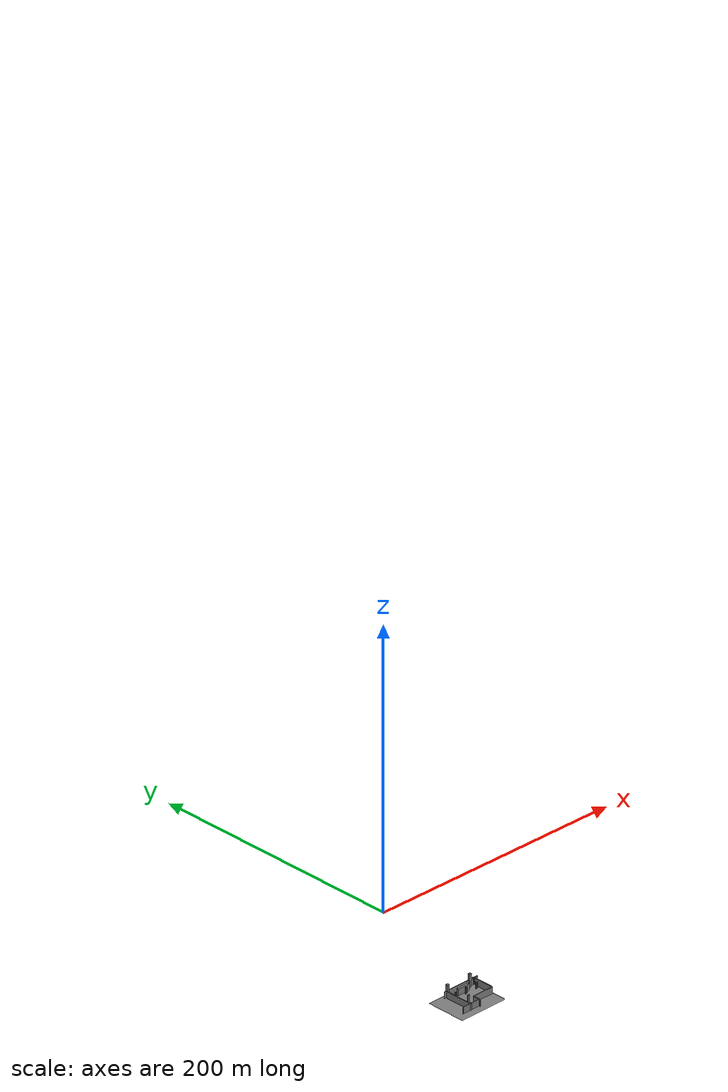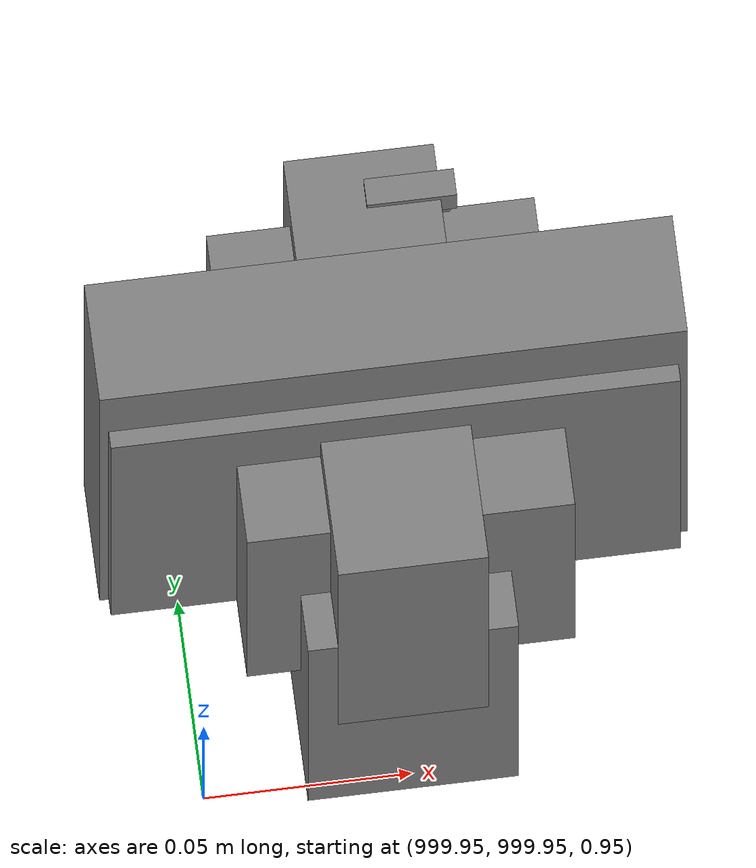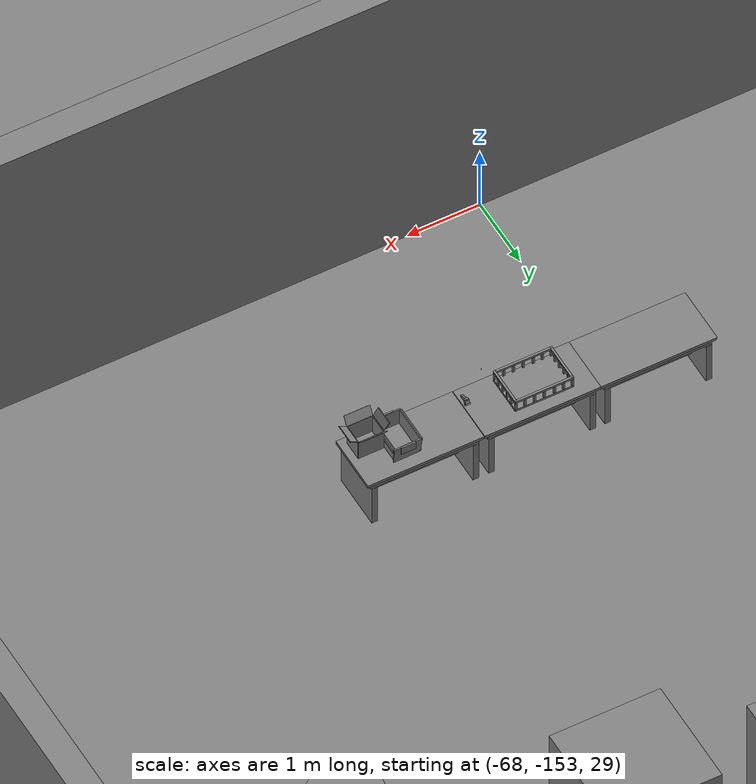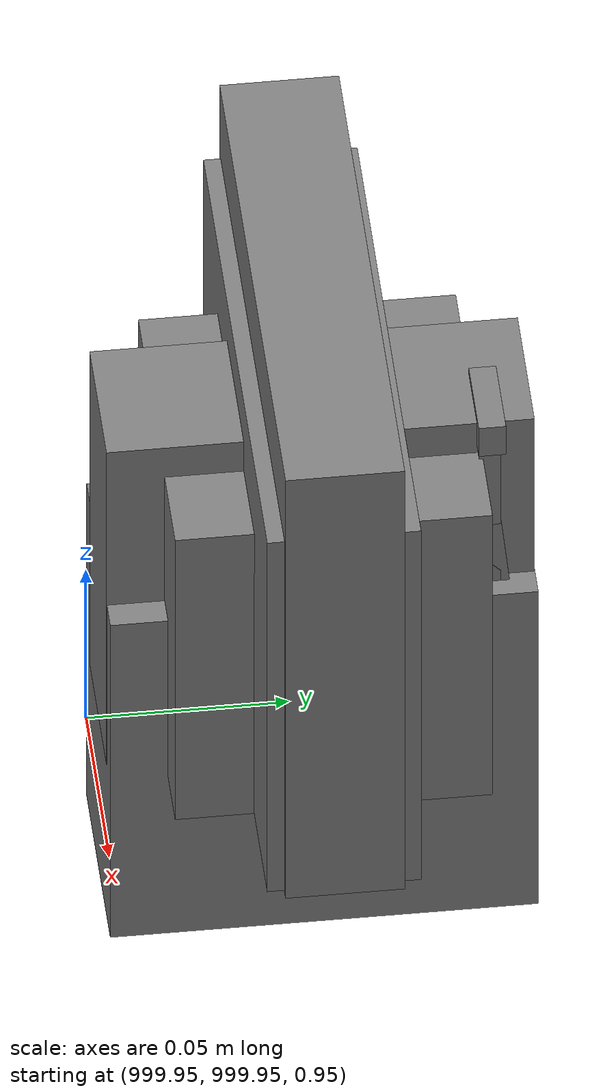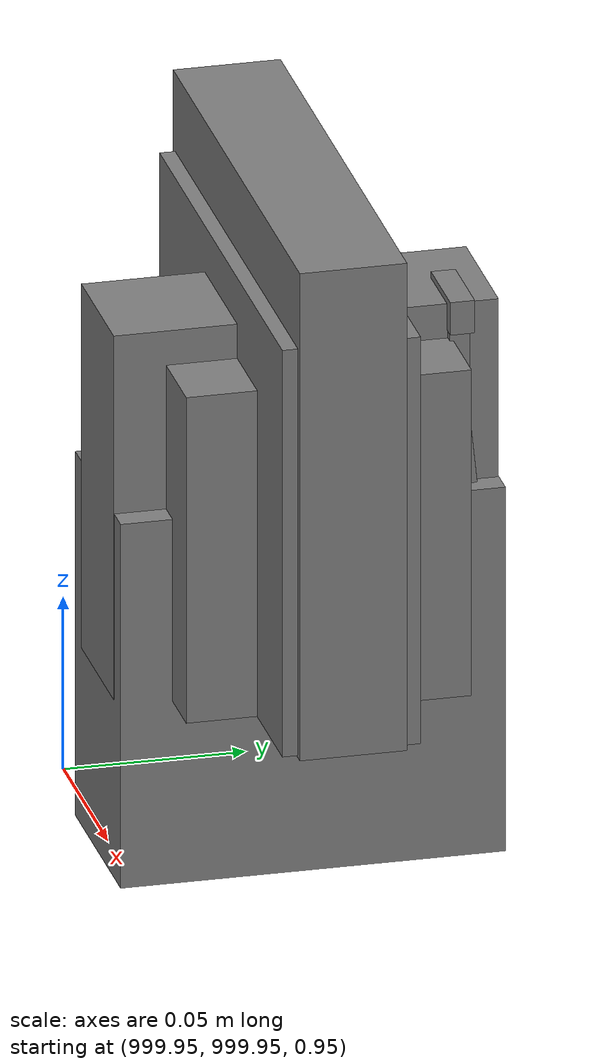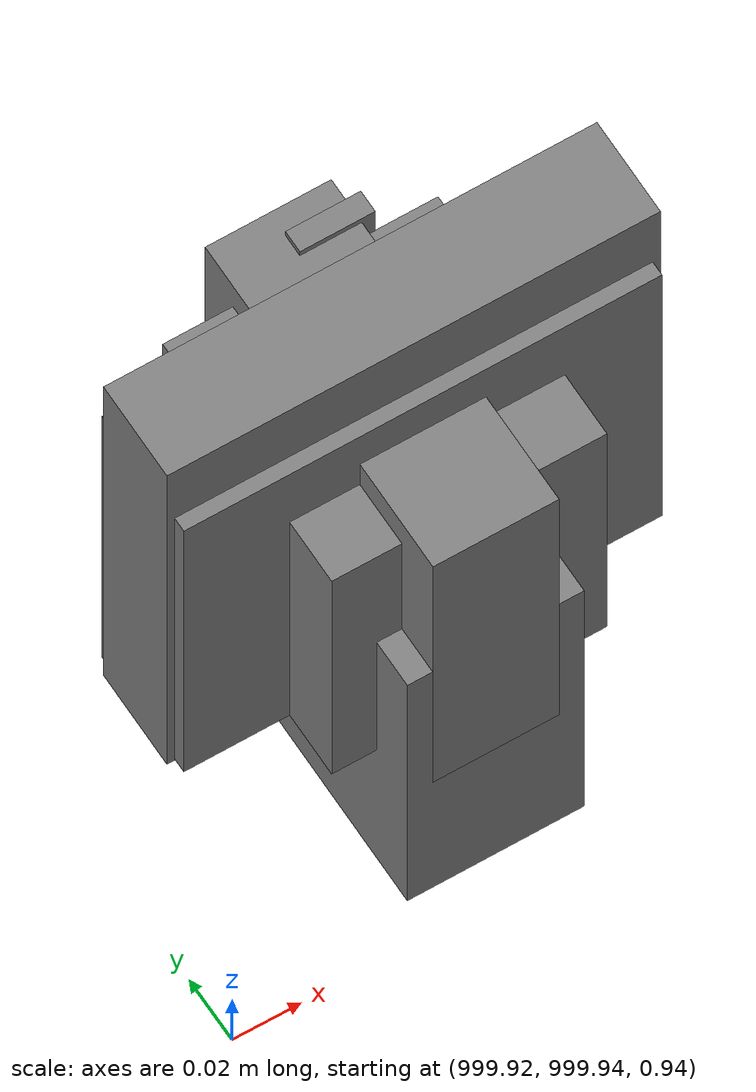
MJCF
<mujoco>
    <option gravity="0.000000000 0.000000000 -9.810000420" timestep="0.0049999999" integrator="implicitfast" density="1.225" viscosity="1.8000001e-05" noslip_iterations="10" iterations="100" sdf_iterations="50">
        <flag multiccd="disable"/>
    </option>
    <size memory="1000M"/>
    <compiler coordinate="local"/>
    <worldbody>
        <light cutoff="30" pos="0 1 1" dir="0 -1 -2"/>
        <light cutoff="30" pos="0 -1 1" dir="0 1 -2"/>
        <body pos="-64.866622925 -149.383972168 30.183746338" euler="89.999984741 89.999946594 0.000000000" name="openloong_gripper_2f85_fix_base_usda_bluebox_01">
            <geom contype="1" conaffinity="1" density="1000" type="box" material="" rgba="0.500000000 0.500000000 0.500000000 1.000000000" solimp="0.899999976 0.949999988 0.001000000" friction="1.000000000 0.005000000 0.000100000" solref="0.020000000 1.000000000" margin="0" condim="3" group="0" pos="0.276580811 0.187225342 0.000068665" quat="0.707106948 0.000077471 0.707106352 0.000077486" size="0.100000001 0.057999998 0.010000000" name="openloong_gripper_2f85_fix_base_usda_geom_444CDDFA_F3CA_4CA2_AF01_26A7CBAE35E6"/>
            <geom contype="1" conaffinity="1" density="1000" type="box" material="" rgba="0.500000000 0.500000000 0.500000000 1.000000000" solimp="0.899999976 0.949999988 0.001000000" friction="1.000000000 0.005000000 0.000100000" solref="0.020000000 1.000000000" margin="0" condim="3" group="0" pos="0.000000000 0.002883911 0.000000000" quat="0.999999881 0.000000000 0.000000000 0.000000000" size="0.254000008 0.003000000 0.172000006" name="openloong_gripper_2f85_fix_base_usda_geom_0FBC531D_0F0C_4942_A70A_705955F1F93D"/>
            <geom contype="1" conaffinity="1" density="1000" type="box" material="" rgba="0.500000000 0.500000000 0.500000000 1.000000000" solimp="0.899999976 0.949999988 0.001000000" friction="1.000000000 0.005000000 0.000100000" solref="0.020000000 1.000000000" margin="0" condim="3" group="0" pos="0.000000000 0.124874115 0.173484802" quat="0.999796331 0.020176515 -0.000000015 0.000000030" size="0.259999990 0.119999997 0.007000000" name="openloong_gripper_2f85_fix_base_usda_geom_2AAAF595_4881_42B2_BB47_7865DA8267BB"/>
            <geom contype="1" conaffinity="1" density="1000" type="box" material="" rgba="0.500000000 0.500000000 0.500000000 1.000000000" solimp="0.899999976 0.949999988 0.001000000" friction="1.000000000 0.005000000 0.000100000" solref="0.020000000 1.000000000" margin="0" condim="3" group="0" pos="0.000000000 0.124874115 -0.173469543" quat="0.999796331 -0.020176545 -0.000000015 0.000000000" size="0.259999990 0.119999997 0.007000000" name="openloong_gripper_2f85_fix_base_usda_geom_CDFED426_655D_42EC_AE65_FADF49CB3D36"/>
            <geom contype="1" conaffinity="1" density="1000" type="box" material="" rgba="0.500000000 0.500000000 0.500000000 1.000000000" solimp="0.899999976 0.949999988 0.001000000" friction="1.000000000 0.005000000 0.000100000" solref="0.020000000 1.000000000" margin="0" condim="3" group="0" pos="0.000000000 0.214008331 0.188980103" quat="0.999912977 0.013176724 0.000000015 0.000000000" size="0.259999990 0.029999999 0.012500000" name="openloong_gripper_2f85_fix_base_usda_geom_6435ADEA_95B4_4AC2_97E7_B222B0672E26"/>
            <geom contype="1" conaffinity="1" density="1000" type="box" material="" rgba="0.500000000 0.500000000 0.500000000 1.000000000" solimp="0.899999976 0.949999988 0.001000000" friction="1.000000000 0.005000000 0.000100000" solref="0.020000000 1.000000000" margin="0" condim="3" group="0" pos="-0.258361816 0.125289917 0.001876831" quat="0.702796936 -0.020792112 0.710783124 0.020769298" size="0.189999998 0.119999997 0.009000000" name="openloong_gripper_2f85_fix_base_usda_geom_B335E83C_026F_43BD_95D8_49EF36A9DF64"/>
            <geom contype="1" conaffinity="1" density="1000" type="box" material="" rgba="0.500000000 0.500000000 0.500000000 1.000000000" solimp="0.899999976 0.949999988 0.001000000" friction="1.000000000 0.005000000 0.000100000" solref="0.020000000 1.000000000" margin="0" condim="3" group="0" pos="0.000000000 0.214008331 -0.188980103" quat="0.999912977 -0.013176769 0.000000030 0.000000015" size="0.259999990 0.029999999 0.012500000" name="openloong_gripper_2f85_fix_base_usda_geom_29FE0C84_16BC_4A5F_B8DB_D8EA312D172C"/>
            <geom contype="1" conaffinity="1" density="1000" type="box" material="" rgba="0.500000000 0.500000000 0.500000000 1.000000000" solimp="0.899999976 0.949999988 0.001000000" friction="1.000000000 0.005000000 0.000100000" solref="0.020000000 1.000000000" margin="0" condim="3" group="0" pos="-0.276611328 0.187225342 0.000068665" quat="0.707106650 0.000077441 0.707106709 0.000077456" size="0.100000001 0.057999998 0.010000000" name="openloong_gripper_2f85_fix_base_usda_geom_1192C894_1678_4FD0_AE86_AC63A3190A35"/>
            <geom contype="1" conaffinity="1" density="1000" type="box" material="" rgba="0.500000000 0.500000000 0.500000000 1.000000000" solimp="0.899999976 0.949999988 0.001000000" friction="1.000000000 0.005000000 0.000100000" solref="0.020000000 1.000000000" margin="0" condim="3" group="0" pos="0.258331299 0.125289917 0.001876831" quat="0.702851415 0.018856421 0.710823774 -0.019329369" size="0.189999998 0.119999997 0.009000000" name="openloong_gripper_2f85_fix_base_usda_geom_976E667F_8394_4509_8BC6_449C6575B19C"/>
            <freejoint name="openloong_gripper_2f85_fix_base_usda_bluebox_01_joint"/>
            <site size="0.005000000 0.005000000 0.005000000" rgba="0.500000000 0.500000000 0.500000000 1.000000000" pos="0.000000000 0.000000000 0.000000000" quat="0.999961913 0.008726534 0.000000000 0.000000000" group="0" type="sphere" name="openloong_gripper_2f85_fix_base_usda_bluebox_01site"/>
        </body>
        <body pos="-64.496299744 -149.491867065 30.235729218" euler="0.000000000 0.000000000 89.999946594" name="openloong_gripper_2f85_fix_base_usda_cardboardbox_01">
            <geom contype="1" conaffinity="1" density="1000" type="box" material="" rgba="0.500000000 0.500000000 0.500000000 1.000000000" solimp="0.899999976 0.949999988 0.001000000" friction="1.000000000 0.005000000 0.000100000" solref="0.020000000 1.000000000" margin="0" condim="3" group="0" pos="-0.003166199 -0.004086494 0.005052090" quat="1.000000000 0.000000000 0.000000000 0.000000000" size="0.142499998 0.177500010 0.005000000" name="openloong_gripper_2f85_fix_base_usda_geom_625B57BF_6C90_4B93_96AF_49344AD83E3F"/>
            <geom contype="1" conaffinity="1" density="1000" type="box" material="" rgba="0.500000000 0.500000000 0.500000000 1.000000000" solimp="0.899999976 0.949999988 0.001000000" friction="1.000000000 0.005000000 0.000100000" solref="0.020000000 1.000000000" margin="0" condim="3" group="0" pos="-0.003166199 0.170316696 0.150570869" quat="1.000000000 0.000000000 0.000000000 0.000000000" size="0.142499998 0.005000000 0.149999991" name="openloong_gripper_2f85_fix_base_usda_geom_961E37BD_2967_4AF6_9038_6E9FBB4AB8D6"/>
            <geom contype="1" conaffinity="1" density="1000" type="box" material="" rgba="0.500000000 0.500000000 0.500000000 1.000000000" solimp="0.899999976 0.949999988 0.001000000" friction="1.000000000 0.005000000 0.000100000" solref="0.020000000 1.000000000" margin="0" condim="3" group="0" pos="-0.147399902 -0.005307198 0.150570869" quat="1.000000000 0.000000000 0.000000000 0.000000000" size="0.005000000 0.177500010 0.149999991" name="openloong_gripper_2f85_fix_base_usda_geom_46D32B53_0938_4A0C_A6B2_6CBDE2752BEE"/>
            <geom contype="1" conaffinity="1" density="1000" type="box" material="" rgba="0.500000000 0.500000000 0.500000000 1.000000000" solimp="0.899999976 0.949999988 0.001000000" friction="1.000000000 0.005000000 0.000100000" solref="0.020000000 1.000000000" margin="0" condim="3" group="0" pos="0.140275955 -0.005307198 0.150570869" quat="1.000000000 0.000000000 0.000000000 0.000000000" size="0.005000000 0.177500010 0.149999991" name="openloong_gripper_2f85_fix_base_usda_geom_1BFDDE3A_8604_4B7B_BB46_83EFE1214A67"/>
            <geom contype="1" conaffinity="1" density="1000" type="box" material="" rgba="0.500000000 0.500000000 0.500000000 1.000000000" solimp="0.899999976 0.949999988 0.001000000" friction="1.000000000 0.005000000 0.000100000" solref="0.020000000 1.000000000" margin="0" condim="3" group="0" pos="-0.003166199 -0.181550980 0.150570869" quat="1.000000000 0.000000000 0.000000000 0.000000000" size="0.142499998 0.005000000 0.149999991" name="openloong_gripper_2f85_fix_base_usda_geom_E4295B4D_D054_4F48_893B_02784F7D954C"/>
            <freejoint name="openloong_gripper_2f85_fix_base_usda_cardboardbox_01_joint"/>
            <site size="0.005000000 0.005000000 0.005000000" rgba="0.500000000 0.500000000 0.500000000 1.000000000" pos="0.000000000 0.000000000 0.000000000" quat="0.999961913 0.008726535 0.000000000 0.000000000" group="0" type="sphere" name="openloong_gripper_2f85_fix_base_usda_site_DD091770_9019_4043_8D34_F92DD6AA8D1C"/>
            <body pos="0.139160156 -0.004048347 0.301930904" euler="-179.999954224 49.383502960 179.999954224" name="openloong_gripper_2f85_fix_base_usda_A1_006">
                <geom contype="1" conaffinity="1" density="1000" type="box" material="" rgba="0.500000000 0.500000000 0.500000000 1.000000000" solimp="0.899999976 0.949999988 0.001000000" friction="1.000000000 0.005000000 0.000100000" solref="0.020000000 1.000000000" margin="0" condim="3" group="0" pos="-0.071587563 0.000009537 0.001745224" quat="0.999999881 0.000000000 0.000000000 0.000000000" size="0.071249999 0.179999992 0.002500000" name="openloong_gripper_2f85_fix_base_usda_geom_A7000BE7_76B4_4795_8FC9_4DE03C606A8F"/>
                <joint armature="0" stiffness="0.07" damping="0.0099999998" axis="0.000000 1.000000 0.000000" type="hinge" name="openloong_gripper_2f85_fix_base_usda_A1_006"/>
            </body>
            <body pos="-0.145902634 -0.004086494 0.301938057" euler="-180.000000000 -60.000011444 -180.000000000" name="openloong_gripper_2f85_fix_base_usda_A2_006">
                <geom contype="1" conaffinity="1" density="1000" type="box" material="" rgba="0.500000000 0.500000000 0.500000000 1.000000000" solimp="0.899999976 0.949999988 0.001000000" friction="1.000000000 0.005000000 0.000100000" solref="0.020000000 1.000000000" margin="0" condim="3" group="0" pos="0.071268082 0.000009537 0.002717972" quat="0.000002921 0.000000000 -0.000000030 0.999999881" size="0.071249999 0.179999992 0.002500000" name="openloong_gripper_2f85_fix_base_usda_geom_C367DEEF_BB81_412A_935E_553A40EF1981"/>
                <joint armature="0" stiffness="0.07" damping="0.0099999998" axis="0.000000 1.000000 0.000000" type="hinge" name="openloong_gripper_2f85_fix_base_usda_A2_006"/>
            </body>
            <body pos="-0.003385544 0.175991058 0.301930904" euler="-125.858116150 -0.000004561 0.000002331" name="openloong_gripper_2f85_fix_base_usda_B2_006">
                <geom contype="1" conaffinity="1" density="1000" type="box" material="" rgba="0.500000000 0.500000000 0.500000000 1.000000000" solimp="0.899999976 0.949999988 0.001000000" friction="1.000000000 0.005000000 0.000100000" solref="0.020000000 1.000000000" margin="0" condim="3" group="0" pos="0.000009537 -0.070939064 -0.002470016" quat="0.999614120 0.027776197 -0.000000015 0.000000030" size="0.137500003 0.064999998 0.005000000" name="openloong_gripper_2f85_fix_base_usda_geom_5BFD812D_31AF_4741_971F_BA0949CA208B"/>
                <joint armature="0" stiffness="0.07" damping="0.0099999998" axis="1.000000 0.000000 0.000000" type="hinge" name="openloong_gripper_2f85_fix_base_usda_B2_006"/>
            </body>
            <body pos="-0.003385544 -0.184140205 0.301938057" euler="147.805557251 0.000000000 0.000000000" name="openloong_gripper_2f85_fix_base_usda_B1_006">
                <geom contype="1" conaffinity="1" density="1000" type="box" material="" rgba="0.500000000 0.500000000 0.500000000 1.000000000" solimp="0.899999976 0.949999988 0.001000000" friction="1.000000000 0.005000000 0.000100000" solref="0.020000000 1.000000000" margin="0" condim="3" group="0" pos="-0.000028610 0.070202351 -0.002703667" quat="0.999614179 -0.027776167 0.000000000 0.000000000" size="0.137500003 0.064999998 0.005000000" name="openloong_gripper_2f85_fix_base_usda_geom_93716FDA_39FE_4687_A143_8C0870A67244"/>
                <joint armature="0" stiffness="0.07" damping="0.0099999998" axis="1.000000 0.000000 0.000000" type="hinge" name="openloong_gripper_2f85_fix_base_usda_B1_006"/>
            </body>
        </body>
        <body pos="-65.882858276 -149.481979370 30.229999542" euler="-64.487716675 0.000000000 0.000000000" name="openloong_gripper_2f85_fix_base_usda_Barcode">
            <geom contype="1" conaffinity="1" density="1000" type="box" material="" rgba="0.500000000 0.500000000 0.500000000 1.000000000" solimp="0.899999976 0.949999988 0.001000000" friction="1.000000000 0.005000000 0.000100000" solref="0.020000000 1.000000000" margin="0" condim="3" group="0" pos="0.000000000 0.013038635 0.001419067" quat="0.000000000 0.000000000 0.000000000 1.000000119" size="0.034000002 0.010000000 0.017999999" name="openloong_gripper_2f85_fix_base_usda_geom_D14A9CB2_5C08_436B_A102_E1EF5A5AE634"/>
            <geom contype="1" conaffinity="1" density="1000" type="box" material="" rgba="0.500000000 0.500000000 0.500000000 1.000000000" solimp="0.899999976 0.949999988 0.001000000" friction="1.000000000 0.005000000 0.000100000" solref="0.020000000 1.000000000" margin="0" condim="3" group="0" pos="0.000000000 -0.035301208 -0.007095337" quat="0.000000000 0.000000000 -0.043619365 0.999048233" size="0.028999999 0.010000000 0.020000000" name="openloong_gripper_2f85_fix_base_usda_geom_C36D8EFA_B3A5_465B_8B5D_20F590C57600"/>
            <geom contype="1" conaffinity="1" density="1000" type="box" material="" rgba="0.500000000 0.500000000 0.500000000 1.000000000" solimp="0.899999976 0.949999988 0.001000000" friction="1.000000000 0.005000000 0.000100000" solref="0.020000000 1.000000000" margin="0" condim="3" group="0" pos="0.000000000 -0.043411255 -0.011749268" quat="0.922262907 0.386563420 0.000000000 0.000000000" size="0.026000001 0.010000000 0.020000000" name="openloong_gripper_2f85_fix_base_usda_geom_EFFABAD4_EC24_4237_815C_512B7B43F7AE"/>
            <geom contype="1" conaffinity="1" density="1000" type="box" material="" rgba="0.500000000 0.500000000 0.500000000 1.000000000" solimp="0.899999976 0.949999988 0.001000000" friction="1.000000000 0.005000000 0.000100000" solref="0.020000000 1.000000000" margin="0" condim="3" group="0" pos="0.000000000 -0.016967773 -0.031860352" quat="0.000000000 0.000000000 0.000000000 1.000000119" size="0.008000000 0.010000000 0.013000000" name="openloong_gripper_2f85_fix_base_usda_geom_40E98FB8_C2C6_4E34_859B_8EB4E11E9CD6"/>
            <geom contype="1" conaffinity="1" density="1000" type="box" material="" rgba="0.500000000 0.500000000 0.500000000 1.000000000" solimp="0.899999976 0.949999988 0.001000000" friction="1.000000000 0.005000000 0.000100000" solref="0.020000000 1.000000000" margin="0" condim="3" group="0" pos="0.000000000 -0.001869202 0.000312805" quat="0.953716993 0.300705761 0.000000000 0.000000000" size="0.032000002 0.010000000 0.018999999" name="openloong_gripper_2f85_fix_base_usda_geom_3D4C6DD8_A723_4E5F_B5FE_B8B4561C285A"/>
            <geom contype="1" conaffinity="1" density="1000" type="box" material="" rgba="0.500000000 0.500000000 0.500000000 1.000000000" solimp="0.899999976 0.949999988 0.001000000" friction="1.000000000 0.005000000 0.000100000" solref="0.020000000 1.000000000" margin="0" condim="3" group="0" pos="0.000000000 -0.019531250 -0.003173828" quat="0.953716993 0.300705761 0.000000000 0.000000000" size="0.030999999 0.010000000 0.020000000" name="openloong_gripper_2f85_fix_base_usda_geom_47E9993A_8D9B_47B5_8137_BACA7852E174"/>
            <geom contype="1" conaffinity="1" density="1000" type="box" material="" rgba="0.500000000 0.500000000 0.500000000 1.000000000" solimp="0.899999976 0.949999988 0.001000000" friction="1.000000000 0.005000000 0.000100000" solref="0.020000000 1.000000000" margin="0" condim="3" group="0" pos="0.000000000 -0.035301208 -0.007095337" quat="0.953716993 0.300705761 0.000000000 0.000000000" size="0.028999999 0.010000000 0.020000000" name="openloong_gripper_2f85_fix_base_usda_geom_F258C7E3_4E62_41B1_BA02_E5784BD21BFA"/>
            <geom contype="1" conaffinity="1" density="1000" type="box" material="" rgba="0.500000000 0.500000000 0.500000000 1.000000000" solimp="0.899999976 0.949999988 0.001000000" friction="1.000000000 0.005000000 0.000100000" solref="0.020000000 1.000000000" margin="0" condim="3" group="0" pos="0.000000000 -0.042617798 -0.071121216" quat="0.000000000 0.000000000 0.000000000 1.000000119" size="0.013000000 0.021000000 0.059999999" name="openloong_gripper_2f85_fix_base_usda_geom_C757430C_645B_4A70_B968_1B2BC8F93255"/>
            <freejoint name="openloong_gripper_2f85_fix_base_usda_Barcode_joint"/>
            <site size="0.005000000 0.005000000 0.005000000" rgba="0.500000000 0.500000000 0.500000000 1.000000000" pos="0.000000000 0.000000000 0.000000000" quat="1.000000000 0.000000000 0.000000000 0.000000000" group="0" type="sphere" name="openloong_gripper_2f85_fix_base_usda_Barcode_site"/>
        </body>
        <body pos="-66.745018005 -149.392349243 30.184000015" euler="0.000000000 0.000000000 89.999946594" name="[22331936087510]_Basket_01">
            <geom contype="1" conaffinity="1" density="1000" type="box" material="" rgba="0.500000000 0.500000000 0.500000000 1.000000000" solimp="0.899999976 0.949999988 0.001000000" friction="1.000000000 0.005000000 0.000100000" solref="0.020000000 1.000000000" margin="0" condim="3" group="0" pos="-0.052425385 0.389207840 0.089787483" quat="0.707107008 0.000000000 0.000000000 0.707106411" size="0.014249999 0.014249999 0.059999999" name="[22331936087510]_geom_FA4C1A91_DABC_4F35_A51E_C33528414D31"/>
            <geom contype="1" conaffinity="1" density="1000" type="box" material="" rgba="0.500000000 0.500000000 0.500000000 1.000000000" solimp="0.899999976 0.949999988 0.001000000" friction="1.000000000 0.005000000 0.000100000" solref="0.020000000 1.000000000" margin="0" condim="3" group="0" pos="0.264015198 -0.133043289 0.089787483" quat="0.707107008 0.000000000 0.000000000 0.707106411" size="0.014249999 0.014249999 0.059999999" name="[22331936087510]_geom_09C53B9D_FB67_4483_B2FC_437532F8787C"/>
            <geom contype="1" conaffinity="1" density="1000" type="box" material="" rgba="0.500000000 0.500000000 0.500000000 1.000000000" solimp="0.899999976 0.949999988 0.001000000" friction="1.000000000 0.005000000 0.000100000" solref="0.020000000 1.000000000" margin="0" condim="3" group="0" pos="-0.264015198 -0.265548706 0.089793205" quat="0.707107008 0.000000000 0.000000000 0.707106411" size="0.014249999 0.014249999 0.059999999" name="[22331936087510]_geom_947C792E_7476_44ED_87AB_1D085C85295E"/>
            <geom contype="1" conaffinity="1" density="1000" type="box" material="" rgba="0.500000000 0.500000000 0.500000000 1.000000000" solimp="0.899999976 0.949999988 0.001000000" friction="1.000000000 0.005000000 0.000100000" solref="0.020000000 1.000000000" margin="0" condim="3" group="0" pos="-0.160263062 -0.389322281 0.089793205" quat="0.707107008 0.000000000 0.000000000 0.707106411" size="0.014249999 0.014249999 0.059999999" name="[22331936087510]_geom_74E22A9D_E6ED_4FCC_BE94_24690143778B"/>
            <geom contype="1" conaffinity="1" density="1000" type="box" material="" rgba="0.500000000 0.500000000 0.500000000 1.000000000" solimp="0.899999976 0.949999988 0.001000000" friction="1.000000000 0.005000000 0.000100000" solref="0.020000000 1.000000000" margin="0" condim="3" group="0" pos="0.162265778 -0.389322281 0.089787483" quat="0.707107008 0.000000000 0.000000000 0.707106411" size="0.014249999 0.014249999 0.059999999" name="[22331936087510]_geom_4A45AD62_2A5A_4F4B_84F5_925BD93BC22B"/>
            <geom contype="1" conaffinity="1" density="1000" type="box" material="" rgba="0.500000000 0.500000000 0.500000000 1.000000000" solimp="0.899999976 0.949999988 0.001000000" friction="1.000000000 0.005000000 0.000100000" solref="0.020000000 1.000000000" margin="0" condim="3" group="0" pos="0.264015198 0.389207840 0.089787483" quat="0.707107008 0.000000000 0.000000000 0.707106411" size="0.014249999 0.014249999 0.059999999" name="[22331936087510]_geom_CBBABCBA_DFF9_4077_B6A8_10D740AAB13A"/>
            <geom contype="1" conaffinity="1" density="1000" type="box" material="" rgba="0.500000000 0.500000000 0.500000000 1.000000000" solimp="0.899999976 0.949999988 0.001000000" friction="1.000000000 0.005000000 0.000100000" solref="0.020000000 1.000000000" margin="0" condim="3" group="0" pos="-0.264015198 -0.133043289 0.089793205" quat="0.707107008 0.000000000 0.000000000 0.707106411" size="0.014249999 0.014249999 0.059999999" name="[22331936087510]_geom_253FD3F3_D5E5_451A_95B8_0B658F8BBD99"/>
            <geom contype="1" conaffinity="1" density="1000" type="box" material="" rgba="0.500000000 0.500000000 0.500000000 1.000000000" solimp="0.899999976 0.949999988 0.001000000" friction="1.000000000 0.005000000 0.000100000" solref="0.020000000 1.000000000" margin="0" condim="3" group="0" pos="-0.264026642 0.269256592 0.089793205" quat="0.707107008 0.000000000 0.000000000 0.707106411" size="0.014249999 0.014249999 0.059999999" name="[22331936087510]_geom_3FD5D3D0_91DC_4530_B077_48826CCA11C8"/>
            <geom contype="1" conaffinity="1" density="1000" type="box" material="" rgba="0.500000000 0.500000000 0.500000000 1.000000000" solimp="0.899999976 0.949999988 0.001000000" friction="1.000000000 0.005000000 0.000100000" solref="0.020000000 1.000000000" margin="0" condim="3" group="0" pos="0.054462433 0.389207840 0.089787483" quat="0.707107008 0.000000000 0.000000000 0.707106411" size="0.014249999 0.014249999 0.059999999" name="[22331936087510]_geom_F7C35CB4_D676_4412_BE05_A455B022724D"/>
            <geom contype="1" conaffinity="1" density="1000" type="box" material="" rgba="0.500000000 0.500000000 0.500000000 1.000000000" solimp="0.899999976 0.949999988 0.001000000" friction="1.000000000 0.005000000 0.000100000" solref="0.020000000 1.000000000" margin="0" condim="3" group="0" pos="0.054462433 -0.389322281 0.089787483" quat="0.707107008 0.000000000 0.000000000 0.707106411" size="0.014249999 0.014249999 0.059999999" name="[22331936087510]_geom_826C2785_68D0_4E24_8E24_85C601CD8384"/>
            <geom contype="1" conaffinity="1" density="1000" type="box" material="" rgba="0.500000000 0.500000000 0.500000000 1.000000000" solimp="0.899999976 0.949999988 0.001000000" friction="1.000000000 0.005000000 0.000100000" solref="0.020000000 1.000000000" margin="0" condim="3" group="0" pos="0.264015198 0.269256592 0.089793205" quat="0.707107008 0.000000000 0.000000000 0.707106411" size="0.014249999 0.014249999 0.059999999" name="[22331936087510]_geom_F6778050_8968_4173_96DB_E017FDDD3A95"/>
            <geom contype="1" conaffinity="1" density="1000" type="box" material="" rgba="0.500000000 0.500000000 0.500000000 1.000000000" solimp="0.899999976 0.949999988 0.001000000" friction="1.000000000 0.005000000 0.000100000" solref="0.020000000 1.000000000" margin="0" condim="3" group="0" pos="0.264015198 -0.389322281 0.089787483" quat="0.707107008 0.000000000 0.000000000 0.707106411" size="0.014249999 0.014249999 0.059999999" name="[22331936087510]_geom_D3E17B06_7A09_4726_B90C_7935CE088C6D"/>
            <geom contype="1" conaffinity="1" density="1000" type="box" material="" rgba="0.500000000 0.500000000 0.500000000 1.000000000" solimp="0.899999976 0.949999988 0.001000000" friction="1.000000000 0.005000000 0.000100000" solref="0.020000000 1.000000000" margin="0" condim="3" group="0" pos="0.000000000 0.000000000 0.015998840" quat="0.707107008 0.000000000 0.000000000 0.707106411" size="0.403499991 0.279000014 0.015750000" name="[22331936087510]_geom_CEDADFD1_E0C3_4AA8_B161_31CC12792F59"/>
            <geom contype="1" conaffinity="1" density="1000" type="box" material="" rgba="0.500000000 0.500000000 0.500000000 1.000000000" solimp="0.899999976 0.949999988 0.001000000" friction="1.000000000 0.005000000 0.000100000" solref="0.020000000 1.000000000" margin="0" condim="3" group="0" pos="0.000000000 -0.389476776 0.163619041" quat="0.707107008 0.000000000 0.000000000 0.707106411" size="0.015000000 0.277500004 0.015750000" name="[22331936087510]_geom_5CC1C6EC_4E36_4E59_96E9_53A32B51DA16"/>
            <geom contype="1" conaffinity="1" density="1000" type="box" material="" rgba="0.500000000 0.500000000 0.500000000 1.000000000" solimp="0.899999976 0.949999988 0.001000000" friction="1.000000000 0.005000000 0.000100000" solref="0.020000000 1.000000000" margin="0" condim="3" group="0" pos="0.162265778 0.389207840 0.089787483" quat="0.707107008 0.000000000 0.000000000 0.707106411" size="0.014249999 0.014249999 0.059999999" name="[22331936087510]_geom_95361E33_7FFC_4C47_952A_434C543AB673"/>
            <geom contype="1" conaffinity="1" density="1000" type="box" material="" rgba="0.500000000 0.500000000 0.500000000 1.000000000" solimp="0.899999976 0.949999988 0.001000000" friction="1.000000000 0.005000000 0.000100000" solref="0.020000000 1.000000000" margin="0" condim="3" group="0" pos="0.000000000 0.389471054 0.163619041" quat="0.707107008 0.000000000 0.000000000 0.707106411" size="0.015000000 0.277500004 0.015750000" name="[22331936087510]_geom_86E5456B_BAC2_46E7_B1B2_FCD9D1B9B211"/>
            <geom contype="1" conaffinity="1" density="1000" type="box" material="" rgba="0.500000000 0.500000000 0.500000000 1.000000000" solimp="0.899999976 0.949999988 0.001000000" friction="1.000000000 0.005000000 0.000100000" solref="0.020000000 1.000000000" margin="0" condim="3" group="0" pos="-0.263511658 0.000000000 0.163619041" quat="0.707107008 0.000000000 0.000000000 0.707106411" size="0.403499991 0.015000000 0.015750000" name="[22331936087510]_geom_419C2B48_AA9A_4985_A3A2_426A6B6270A5"/>
            <geom contype="1" conaffinity="1" density="1000" type="box" material="" rgba="0.500000000 0.500000000 0.500000000 1.000000000" solimp="0.899999976 0.949999988 0.001000000" friction="1.000000000 0.005000000 0.000100000" solref="0.020000000 1.000000000" margin="0" condim="3" group="0" pos="-0.264015198 0.141334534 0.089793205" quat="0.707107008 0.000000000 0.000000000 0.707106411" size="0.014249999 0.014249999 0.059999999" name="[22331936087510]_geom_304ED39E_8F56_40C9_8A57_18A1F05AE0DC"/>
            <geom contype="1" conaffinity="1" density="1000" type="box" material="" rgba="0.500000000 0.500000000 0.500000000 1.000000000" solimp="0.899999976 0.949999988 0.001000000" friction="1.000000000 0.005000000 0.000100000" solref="0.020000000 1.000000000" margin="0" condim="3" group="0" pos="0.264015198 -0.265548706 0.089787483" quat="0.707107008 0.000000000 0.000000000 0.707106411" size="0.014249999 0.014249999 0.059999999" name="[22331936087510]_geom_24E851BF_7253_41B2_B4BF_5EB3608120C4"/>
            <geom contype="1" conaffinity="1" density="1000" type="box" material="" rgba="0.500000000 0.500000000 0.500000000 1.000000000" solimp="0.899999976 0.949999988 0.001000000" friction="1.000000000 0.005000000 0.000100000" solref="0.020000000 1.000000000" margin="0" condim="3" group="0" pos="-0.160263062 0.389207840 0.089787483" quat="0.707107008 0.000000000 0.000000000 0.707106411" size="0.014249999 0.014249999 0.059999999" name="[22331936087510]_geom_991C0D23_4D73_487E_9580_9948775F89CB"/>
            <geom contype="1" conaffinity="1" density="1000" type="box" material="" rgba="0.500000000 0.500000000 0.500000000 1.000000000" solimp="0.899999976 0.949999988 0.001000000" friction="1.000000000 0.005000000 0.000100000" solref="0.020000000 1.000000000" margin="0" condim="3" group="0" pos="-0.052425385 -0.389322281 0.089787483" quat="0.707107008 0.000000000 0.000000000 0.707106411" size="0.014249999 0.014249999 0.059999999" name="[22331936087510]_geom_97F29A53_1D79_4781_9EA0_981DA51237B6"/>
            <geom contype="1" conaffinity="1" density="1000" type="box" material="" rgba="0.500000000 0.500000000 0.500000000 1.000000000" solimp="0.899999976 0.949999988 0.001000000" friction="1.000000000 0.005000000 0.000100000" solref="0.020000000 1.000000000" margin="0" condim="3" group="0" pos="-0.264026642 -0.389322281 0.089793205" quat="0.707107008 0.000000000 0.000000000 0.707106411" size="0.014249999 0.014249999 0.059999999" name="[22331936087510]_geom_52850D9A_6D84_4840_BD5B_3BAD4B022E2D"/>
            <geom contype="1" conaffinity="1" density="1000" type="box" material="" rgba="0.500000000 0.500000000 0.500000000 1.000000000" solimp="0.899999976 0.949999988 0.001000000" friction="1.000000000 0.005000000 0.000100000" solref="0.020000000 1.000000000" margin="0" condim="3" group="0" pos="0.264015198 0.141334534 0.089787483" quat="0.707107008 0.000000000 0.000000000 0.707106411" size="0.014249999 0.014249999 0.059999999" name="[22331936087510]_geom_5BD2E821_FAB3_4AC4_B8A0_80C13C8749B9"/>
            <geom contype="1" conaffinity="1" density="1000" type="box" material="" rgba="0.500000000 0.500000000 0.500000000 1.000000000" solimp="0.899999976 0.949999988 0.001000000" friction="1.000000000 0.005000000 0.000100000" solref="0.020000000 1.000000000" margin="0" condim="3" group="0" pos="-0.264015198 0.389207840 0.089793205" quat="0.707107008 0.000000000 0.000000000 0.707106411" size="0.014249999 0.014249999 0.059999999" name="[22331936087510]_geom_70EF95FC_0B77_4F75_97A6_D77C3C1ADE34"/>
            <geom contype="1" conaffinity="1" density="1000" type="box" material="" rgba="0.500000000 0.500000000 0.500000000 1.000000000" solimp="0.899999976 0.949999988 0.001000000" friction="1.000000000 0.005000000 0.000100000" solref="0.020000000 1.000000000" margin="0" condim="3" group="0" pos="0.264015198 0.004480362 0.089787483" quat="0.707107008 0.000000000 0.000000000 0.707106411" size="0.014249999 0.014249999 0.059999999" name="[22331936087510]_geom_B2BB0140_173F_495F_B343_46E2DEFCB782"/>
            <geom contype="1" conaffinity="1" density="1000" type="box" material="" rgba="0.500000000 0.500000000 0.500000000 1.000000000" solimp="0.899999976 0.949999988 0.001000000" friction="1.000000000 0.005000000 0.000100000" solref="0.020000000 1.000000000" margin="0" condim="3" group="0" pos="0.263694763 -0.000011444 0.163619041" quat="0.707107008 0.000000000 0.000000000 0.707106411" size="0.403499991 0.015000000 0.015750000" name="[22331936087510]_geom_7409DE76_D4F1_4A44_A929_7255FB1D1C09"/>
            <geom contype="1" conaffinity="1" density="1000" type="box" material="" rgba="0.500000000 0.500000000 0.500000000 1.000000000" solimp="0.899999976 0.949999988 0.001000000" friction="1.000000000 0.005000000 0.000100000" solref="0.020000000 1.000000000" margin="0" condim="3" group="0" pos="-0.264015198 0.004480362 0.089793205" quat="0.707107008 0.000000000 0.000000000 0.707106411" size="0.014249999 0.014249999 0.059999999" name="[22331936087510]_geom_27436EC8_73D6_4D36_8917_7680C9F3CB7F"/>
            <freejoint name="[22331936087510]_joint_9444623D_84A9_4DDB_AFEC_8F14E98BC822"/>
        </body>
        <body pos="0.000000000 0.000000000 0.000000000" euler="0.000000000 0.000000000 0.000000000" name="Static Objects_Static Objects">
            <geom contype="1" conaffinity="1" density="1000" type="box" material="" rgba="0.500000000 0.500000000 0.500000000 1.000000000" solimp="0.899999976 0.949999988 0.001000000" friction="1.000000000 0.005000000 0.000100000" solref="0.020000000 1.000000000" margin="0" condim="3" group="0" pos="-67.544113159 -149.365814209 29.727830887" quat="0.500000417 0.499999970 0.499999553 0.499999970" size="0.381000012 0.319999993 0.041000001" name="Static Objects_geom_67542C56_844A_423D_8CAE_018BBD8EEAEC"/>
            <geom contype="1" conaffinity="1" density="1000" type="box" material="" rgba="0.500000000 0.500000000 0.500000000 1.000000000" solimp="0.899999976 0.949999988 0.001000000" friction="1.000000000 0.005000000 0.000100000" solref="0.020000000 1.000000000" margin="0" condim="3" group="0" pos="-68.239501953 -149.365814209 30.086868286" quat="0.500000417 0.499999970 0.499999553 0.499999970" size="0.370999992 0.039500002 0.745000005" name="Static Objects_geom_2A4265A2_F326_460E_ABE7_8D35A0441AA8"/>
            <geom contype="1" conaffinity="1" density="1000" type="box" material="" rgba="0.500000000 0.500000000 0.500000000 1.000000000" solimp="0.899999976 0.949999988 0.001000000" friction="1.000000000 0.005000000 0.000100000" solref="0.020000000 1.000000000" margin="0" condim="3" group="0" pos="-68.239501953 -149.365814209 30.147235870" quat="0.500000417 0.499999970 0.499999553 0.499999970" size="0.400000006 0.022000000 0.800000012" name="Static Objects_geom_E072B95C_4629_4256_ACB1_C7E89DF3AE67"/>
            <geom contype="1" conaffinity="1" density="1000" type="box" material="" rgba="0.500000000 0.500000000 0.500000000 1.000000000" solimp="0.899999976 0.949999988 0.001000000" friction="1.000000000 0.005000000 0.000100000" solref="0.020000000 1.000000000" margin="0" condim="3" group="0" pos="-68.934890747 -149.365814209 29.727830887" quat="0.500000417 0.499999970 0.499999553 0.499999970" size="0.381000012 0.319999993 0.041000001" name="Static Objects_geom_2DAB322F_BC42_4A56_928E_6501CABAB24B"/>
            <geom contype="1" conaffinity="1" density="1000" type="box" material="" rgba="0.500000000 0.500000000 0.500000000 1.000000000" solimp="0.899999976 0.949999988 0.001000000" friction="1.000000000 0.005000000 0.000100000" solref="0.020000000 1.000000000" margin="0" condim="3" group="0" pos="-68.239501953 -149.365814209 29.561563492" quat="0.500000417 0.499999970 0.499999553 0.499999970" size="0.020000000 0.022000000 0.660000026" name="Static Objects_geom_E2BB7409_DEA7_4D86_BE44_58902A009B44"/>
            <geom contype="1" conaffinity="1" density="1000" type="box" material="" rgba="0.500000000 0.500000000 0.500000000 1.000000000" solimp="0.899999976 0.949999988 0.001000000" friction="1.000000000 0.005000000 0.000100000" solref="0.020000000 1.000000000" margin="0" condim="3" group="0" pos="-65.945671082 -149.365814209 29.727830887" quat="0.500000417 0.499999970 0.499999553 0.499999970" size="0.381000012 0.319999993 0.041000001" name="Static Objects_geom_BEB5C7D4_6C79_4829_BE43_76ABA57F7883"/>
            <geom contype="1" conaffinity="1" density="1000" type="box" material="" rgba="0.500000000 0.500000000 0.500000000 1.000000000" solimp="0.899999976 0.949999988 0.001000000" friction="1.000000000 0.005000000 0.000100000" solref="0.020000000 1.000000000" margin="0" condim="3" group="0" pos="-66.641059875 -149.365814209 30.086868286" quat="0.500000417 0.499999970 0.499999553 0.499999970" size="0.370999992 0.039500002 0.745000005" name="Static Objects_geom_201A7DE5_9418_4A5E_BA64_CF63BEFE5AA9"/>
            <geom contype="1" conaffinity="1" density="1000" type="box" material="" rgba="0.500000000 0.500000000 0.500000000 1.000000000" solimp="0.899999976 0.949999988 0.001000000" friction="1.000000000 0.005000000 0.000100000" solref="0.020000000 1.000000000" margin="0" condim="3" group="0" pos="-66.641059875 -149.365814209 30.147235870" quat="0.500000417 0.499999970 0.499999553 0.499999970" size="0.400000006 0.022000000 0.800000012" name="Static Objects_geom_2E058AC2_3A8F_44EA_82C0_3AB522B28129"/>
            <geom contype="1" conaffinity="1" density="1000" type="box" material="" rgba="0.500000000 0.500000000 0.500000000 1.000000000" solimp="0.899999976 0.949999988 0.001000000" friction="1.000000000 0.005000000 0.000100000" solref="0.020000000 1.000000000" margin="0" condim="3" group="0" pos="-67.336448669 -149.365814209 29.727830887" quat="0.500000417 0.499999970 0.499999553 0.499999970" size="0.381000012 0.319999993 0.041000001" name="Static Objects_geom_E5E5EE75_7C4F_45C5_93E8_56F598130921"/>
            <geom contype="1" conaffinity="1" density="1000" type="box" material="" rgba="0.500000000 0.500000000 0.500000000 1.000000000" solimp="0.899999976 0.949999988 0.001000000" friction="1.000000000 0.005000000 0.000100000" solref="0.020000000 1.000000000" margin="0" condim="3" group="0" pos="-66.641059875 -149.365814209 29.561563492" quat="0.500000417 0.499999970 0.499999553 0.499999970" size="0.020000000 0.022000000 0.660000026" name="Static Objects_geom_F2C3F94F_7BC9_402B_A996_3908D50DE866"/>
            <geom contype="1" conaffinity="1" density="1000" type="box" material="" rgba="0.500000000 0.500000000 0.500000000 1.000000000" solimp="0.899999976 0.949999988 0.001000000" friction="1.000000000 0.005000000 0.000100000" solref="0.020000000 1.000000000" margin="0" condim="3" group="0" pos="-64.338577271 -149.365814209 29.727830887" quat="0.500000417 0.499999970 0.499999553 0.499999970" size="0.381000012 0.319999993 0.041000001" name="Static Objects_geom_E946AD30_3389_4383_B6AD_AF6614B3D96F"/>
            <geom contype="1" conaffinity="1" density="1000" type="box" material="" rgba="0.500000000 0.500000000 0.500000000 1.000000000" solimp="0.899999976 0.949999988 0.001000000" friction="1.000000000 0.005000000 0.000100000" solref="0.020000000 1.000000000" margin="0" condim="3" group="0" pos="-65.033966064 -149.365814209 30.086868286" quat="0.500000417 0.499999970 0.499999553 0.499999970" size="0.370999992 0.039500002 0.745000005" name="Static Objects_geom_423D668D_D7A9_49D0_9A2A_8B85D9F863A3"/>
            <geom contype="1" conaffinity="1" density="1000" type="box" material="" rgba="0.500000000 0.500000000 0.500000000 1.000000000" solimp="0.899999976 0.949999988 0.001000000" friction="1.000000000 0.005000000 0.000100000" solref="0.020000000 1.000000000" margin="0" condim="3" group="0" pos="-65.033966064 -149.365814209 30.147235870" quat="0.500000417 0.499999970 0.499999553 0.499999970" size="0.400000006 0.022000000 0.800000012" name="Static Objects_geom_039C9DD1_3A24_493A_A939_05AB8643B6E4"/>
            <geom contype="1" conaffinity="1" density="1000" type="box" material="" rgba="0.500000000 0.500000000 0.500000000 1.000000000" solimp="0.899999976 0.949999988 0.001000000" friction="1.000000000 0.005000000 0.000100000" solref="0.020000000 1.000000000" margin="0" condim="3" group="0" pos="-65.729354858 -149.365814209 29.727830887" quat="0.500000417 0.499999970 0.499999553 0.499999970" size="0.381000012 0.319999993 0.041000001" name="Static Objects_geom_A8E3800A_A2D2_4CF5_9C9F_51EBAAEC086B"/>
            <geom contype="1" conaffinity="1" density="1000" type="box" material="" rgba="0.500000000 0.500000000 0.500000000 1.000000000" solimp="0.899999976 0.949999988 0.001000000" friction="1.000000000 0.005000000 0.000100000" solref="0.020000000 1.000000000" margin="0" condim="3" group="0" pos="-65.033966064 -149.365814209 29.561563492" quat="0.500000417 0.499999970 0.499999553 0.499999970" size="0.020000000 0.022000000 0.660000026" name="Static Objects_geom_34165961_48B3_4C1C_8DB9_5ADC2CE8D140"/>
            <geom contype="1" conaffinity="1" density="1000" type="box" material="" rgba="0.500000000 0.500000000 0.500000000 1.000000000" solimp="0.899999976 0.949999988 0.001000000" friction="1.000000000 0.005000000 0.000100000" solref="0.020000000 1.000000000" margin="0" condim="3" group="0" pos="-61.754566193 -137.853729248 33.906845093" quat="0.707107067 0.000000000 0.000000000 0.707106471" size="0.759999990 0.759999990 4.500000000" name="Static Objects_geom_6838947A_4AD4_4BD9_B351_3E8EE0841296"/>
            <geom contype="1" conaffinity="1" density="1000" type="box" material="" rgba="0.500000000 0.500000000 0.500000000 1.000000000" solimp="0.899999976 0.949999988 0.001000000" friction="1.000000000 0.005000000 0.000100000" solref="0.020000000 1.000000000" margin="0" condim="3" group="0" pos="-57.511135101 -144.927108765 31.707921982" quat="1.000000000 0.000000000 0.000000000 0.000000000" size="0.200000003 8.000000000 2.299999952" name="Static Objects_geom_D24A4305_ABC1_4816_9B4B_095F148AEBE9"/>
            <geom contype="1" conaffinity="1" density="1000" type="box" material="" rgba="0.500000000 0.500000000 0.500000000 1.000000000" solimp="0.899999976 0.949999988 0.001000000" friction="1.000000000 0.005000000 0.000100000" solref="0.020000000 1.000000000" margin="0" condim="3" group="0" pos="-80.517646790 -157.574050903 31.688196182" quat="0.707107067 0.000000000 0.000000000 0.707106471" size="0.600000024 0.600000024 2.299999952" name="Static Objects_geom_47D348F1_8050_4B05_A94B_4E88B3BF1864"/>
            <geom contype="1" conaffinity="1" density="1000" type="box" material="" rgba="0.500000000 0.500000000 0.500000000 1.000000000" solimp="0.899999976 0.949999988 0.001000000" friction="1.000000000 0.005000000 0.000100000" solref="0.020000000 1.000000000" margin="0" condim="3" group="0" pos="-80.711044312 -147.414932251 31.666158676" quat="1.000000000 0.000000000 0.000000000 0.000000000" size="0.200000003 10.000000000 2.299999952" name="Static Objects_geom_69F7C2D1_97F0_416E_9B68_C4C1AB337964"/>
            <geom contype="1" conaffinity="1" density="1000" type="box" material="" rgba="0.500000000 0.500000000 0.500000000 1.000000000" solimp="0.899999976 0.949999988 0.001000000" friction="1.000000000 0.005000000 0.000100000" solref="0.020000000 1.000000000" margin="0" condim="3" group="0" pos="-57.687217712 -137.434692383 31.688196182" quat="0.707107067 0.000000000 0.000000000 0.707106471" size="0.600000024 0.600000024 2.299999952" name="Static Objects_geom_E9AA2B65_843E_4959_9B03_096B3AC393A9"/>
            <geom contype="1" conaffinity="1" density="1000" type="box" material="" rgba="0.500000000 0.500000000 0.500000000 1.000000000" solimp="0.899999976 0.949999988 0.001000000" friction="1.000000000 0.005000000 0.000100000" solref="0.020000000 1.000000000" margin="0" condim="3" group="0" pos="-69.537033081 -140.263229370 31.714921951" quat="0.707107067 0.000000000 0.000000000 0.707106471" size="0.759999990 4.500000000 2.299999952" name="Static Objects_geom_02D775A8_801C_46D9_89DB_68AE0C0AF4BD"/>
            <geom contype="1" conaffinity="1" density="1000" type="box" material="" rgba="0.500000000 0.500000000 0.500000000 1.000000000" solimp="0.899999976 0.949999988 0.001000000" friction="1.000000000 0.005000000 0.000100000" solref="0.020000000 1.000000000" margin="0" condim="3" group="0" pos="-80.073638916 -137.853713989 33.906845093" quat="0.707107067 0.000000000 0.000000000 0.707106471" size="0.759999990 0.759999990 4.500000000" name="Static Objects_geom_A7B9FBBA_D0C2_49A6_AEF8_6B70BF244EA6"/>
            <geom contype="1" conaffinity="1" density="1000" type="box" material="" rgba="0.500000000 0.500000000 0.500000000 1.000000000" solimp="0.899999976 0.949999988 0.001000000" friction="1.000000000 0.005000000 0.000100000" solref="0.020000000 1.000000000" margin="0" condim="3" group="0" pos="-73.406707764 -155.734664917 31.707921982" quat="1.000000000 0.000000000 0.000000000 0.000000000" size="0.200000003 3.000000000 2.299999952" name="Static Objects_geom_2EBBB107_5530_43ED_A8BC_80658D0E13E3"/>
            <geom contype="1" conaffinity="1" density="1000" type="box" material="" rgba="0.500000000 0.500000000 0.500000000 1.000000000" solimp="0.899999976 0.949999988 0.001000000" friction="1.000000000 0.005000000 0.000100000" solref="0.020000000 1.000000000" margin="0" condim="3" group="0" pos="-68.497543335 -137.448257446 31.707921982" quat="0.707107067 0.000000000 0.000000000 0.707106471" size="0.200000003 14.000000000 2.299999952" name="Static Objects_geom_7BF1526B_99C9_4433_8252_B821A121C7FF"/>
            <geom contype="1" conaffinity="1" density="1000" type="cylinder" material="" rgba="0.500000000 0.500000000 0.500000000 1.000000000" solimp="0.899999976 0.949999988 0.001000000" friction="1.000000000 0.005000000 0.000100000" solref="0.020000000 1.000000000" margin="0" condim="3" group="0" pos="-68.868522644 -142.134506226 31.711090088" quat="0.707107067 0.000000000 0.000000000 0.707106471" size="0.509999990 2.299999952 1.000000000" name="Static Objects_geom_91FDC9AE_E0B4_42AC_8136_F8D73C35A0EE"/>
            <geom contype="1" conaffinity="1" density="1000" type="plane" material="" rgba="0.500000000 0.500000000 0.500000000 1.000000000" solimp="0.899999976 0.949999988 0.001000000" friction="1.000000000 0.005000000 0.000100000" solref="0.020000000 1.000000000" margin="0" condim="3" group="0" pos="-72.873703003 -147.131927490 29.409669876" quat="1.000000000 0.000000000 0.000000000 0.000000000" size="18.000000000 14.000000000 1.000000000" name="Static Objects_geom_171C6B55_4F78_46E4_8FE6_FEF680A8A676"/>
            <geom contype="1" conaffinity="1" density="1000" type="box" material="" rgba="0.500000000 0.500000000 0.500000000 1.000000000" solimp="0.899999976 0.949999988 0.001000000" friction="1.000000000 0.005000000 0.000100000" solref="0.020000000 1.000000000" margin="0" condim="3" group="0" pos="-79.943580627 -157.782272339 31.707921982" quat="0.707107067 0.000000000 0.000000000 0.707106471" size="0.200000003 7.000000000 2.299999952" name="Static Objects_geom_2AA7241A_7395_4C8A_B0E2_FF4AE189DDDD"/>
            <geom contype="1" conaffinity="1" density="1000" type="box" material="" rgba="0.500000000 0.500000000 0.500000000 1.000000000" solimp="0.899999976 0.949999988 0.001000000" friction="1.000000000 0.005000000 0.000100000" solref="0.020000000 1.000000000" margin="0" condim="3" group="0" pos="-65.421028137 -152.903442383 31.707921982" quat="0.707107067 0.000000000 0.000000000 0.707106471" size="0.200000003 7.800000191 2.299999952" name="Static Objects_geom_C11F1F7B_73B6_44E3_97DA_CD86553460E1"/>
            <geom contype="1" conaffinity="1" density="1000" type="box" material="" rgba="0.500000000 0.500000000 0.500000000 1.000000000" solimp="0.899999976 0.949999988 0.001000000" friction="1.000000000 0.005000000 0.000100000" solref="0.020000000 1.000000000" margin="0" condim="3" group="0" pos="-74.776908875 -149.964416504 31.688196182" quat="1.000000000 0.000000000 0.000000000 0.000000000" size="0.600000024 0.409999996 2.299999952" name="Static Objects_geom_0E4916EA_15A2_4EDC_83E8_4367CDB5BF0D"/>
            <geom contype="1" conaffinity="1" density="1000" type="cylinder" material="" rgba="0.500000000 0.500000000 0.500000000 1.000000000" solimp="0.899999976 0.949999988 0.001000000" friction="1.000000000 0.005000000 0.000100000" solref="0.020000000 1.000000000" margin="0" condim="3" group="0" pos="-60.161884308 -142.134506226 31.711090088" quat="0.707107067 0.000000000 0.000000000 0.707106471" size="0.509999990 2.299999952 1.000000000" name="Static Objects_geom_CBE501FC_CB23_4454_8819_EBCD6595044B"/>
            <geom contype="1" conaffinity="1" density="1000" type="cylinder" material="" rgba="0.500000000 0.500000000 0.500000000 1.000000000" solimp="0.899999976 0.949999988 0.001000000" friction="1.000000000 0.005000000 0.000100000" solref="0.020000000 1.000000000" margin="0" condim="3" group="0" pos="-75.382453918 -149.963455200 31.711090088" quat="0.707107067 0.000000000 0.000000000 0.707106471" size="0.409999996 2.299999952 1.000000000" name="Static Objects_geom_EE0564CB_E6CC_41E5_87A9_3D6408CFFCB9"/>
            <geom contype="1" conaffinity="1" density="1000" type="cylinder" material="" rgba="0.500000000 0.500000000 0.500000000 1.000000000" solimp="0.899999976 0.949999988 0.001000000" friction="1.000000000 0.005000000 0.000100000" solref="0.020000000 1.000000000" margin="0" condim="3" group="0" pos="-74.154960632 -149.963455200 31.711090088" quat="0.707107067 0.000000000 0.000000000 0.707106471" size="0.409999996 2.299999952 1.000000000" name="Static Objects_geom_8B32A781_613A_4137_94B3_A8917BA9A8D0"/>
            <geom contype="1" conaffinity="1" density="1000" type="cylinder" material="" rgba="0.500000000 0.500000000 0.500000000 1.000000000" solimp="0.899999976 0.949999988 0.001000000" friction="1.000000000 0.005000000 0.000100000" solref="0.020000000 1.000000000" margin="0" condim="3" group="0" pos="-77.566612244 -142.134506226 31.711090088" quat="0.707107067 0.000000000 0.000000000 0.707106471" size="0.509999990 2.299999952 1.000000000" name="Static Objects_geom_C6CD155B_063E_43EE_8267_2E6AD7C77583"/>
        </body>
        <body pos="-65.797348022 -148.908660889 31.167768478" euler="129.189666748 -42.744323730 102.110122681" mocap="true" name="spotlight3_SpotLight"/>
        <body pos="1000.000000000 1000.000000000 1.000000000" euler="0.000011953 0.000005123 -179.999984741" name="openloong_gripper_2f85_fix_base_usda_intel_box">
            <geom contype="1" conaffinity="1" density="1000" type="box" material="" rgba="0.500000000 0.500000000 0.500000000 1.000000000" solimp="0.899999976 0.949999988 0.001000000" friction="1.000000000 0.005000000 0.000100000" solref="0.020000000 1.000000000" margin="0" condim="3" group="0" pos="0.000000000 -0.000067139 0.000082284" quat="0.707106709 0.000000225 0.000000253 0.707106650" size="0.052800003 0.025300000 0.052800003" name="openloong_gripper_2f85_fix_base_usda_geom_15F6716F_CBEB_4DD7_9FC2_52D34E5C92E6"/>
            <freejoint name="openloong_gripper_2f85_fix_base_usda_intel_box_joint"/>
            <site size="0.005000000 0.005000000 0.005000000" rgba="0.500000000 0.500000000 0.500000000 1.000000000" pos="0.000000000 0.000000000 0.000000000" quat="0.999961913 0.008726500 0.000000000 0.000000000" group="0" type="sphere" name="openloong_gripper_2f85_fix_base_usda_intel_boxsite"/>
        </body>
        <body pos="-66.274566650 -149.436782837 31.171518326" euler="173.719650269 4.129373550 -148.547576904" mocap="true" name="spotlight4_SpotLight"/>
        <body pos="1000.000000000 1000.000000000 1.000000000" euler="0.000000000 0.000000000 180.000000000" name="openloong_gripper_2f85_fix_base_usda_battery_01">
            <geom contype="1" conaffinity="1" density="1000" type="box" material="" rgba="0.500000000 0.500000000 0.500000000 1.000000000" solimp="0.899999976 0.949999988 0.001000000" friction="1.000000000 0.005000000 0.000100000" solref="0.020000000 1.000000000" margin="0" condim="3" group="0" pos="-0.011123657 -0.041940309 0.101691343" quat="1.000000000 0.000000000 0.000000000 0.000000000" size="0.010800000 0.003375000 0.004725000" name="openloong_gripper_2f85_fix_base_usda_geom_17D1CA96_9BB1_4F01_989F_EFB27E675A3B"/>
            <geom contype="1" conaffinity="1" density="1000" type="box" material="" rgba="0.500000000 0.500000000 0.500000000 1.000000000" solimp="0.899999976 0.949999988 0.001000000" friction="1.000000000 0.005000000 0.000100000" solref="0.020000000 1.000000000" margin="0" condim="3" group="0" pos="-0.010876465 -0.044247437 0.047066893" quat="0.998702705 -0.050920475 0.000000000 0.000000000" size="0.009450001 0.002700000 0.024975000" name="openloong_gripper_2f85_fix_base_usda_geom_DD3B8104_1433_49AA_B613_B545F75578BC"/>
            <geom contype="1" conaffinity="1" density="1000" type="box" material="" rgba="0.500000000 0.500000000 0.500000000 1.000000000" solimp="0.899999976 0.949999988 0.001000000" friction="1.000000000 0.005000000 0.000100000" solref="0.020000000 1.000000000" margin="0" condim="3" group="0" pos="-0.001235962 -0.000659180 0.047381196" quat="1.000000000 0.000000000 0.000000000 0.000000000" size="0.039420001 0.039150000 0.047250003" name="openloong_gripper_2f85_fix_base_usda_geom_48297852_B028_49A4_BFED_4E1E1CF0A898"/>
            <geom contype="1" conaffinity="1" density="1000" type="box" material="" rgba="0.500000000 0.500000000 0.500000000 1.000000000" solimp="0.899999976 0.949999988 0.001000000" friction="1.000000000 0.005000000 0.000100000" solref="0.020000000 1.000000000" margin="0" condim="3" group="0" pos="-0.010876465 -0.039138794 0.009851727" quat="1.000000000 0.000000000 0.000000000 0.000000000" size="0.009450001 0.010800000 0.013500000" name="openloong_gripper_2f85_fix_base_usda_geom_3E7D70FE_F005_4F2A_8007_2DFD5B36E157"/>
            <geom contype="1" conaffinity="1" density="1000" type="box" material="" rgba="0.500000000 0.500000000 0.500000000 1.000000000" solimp="0.899999976 0.949999988 0.001000000" friction="1.000000000 0.005000000 0.000100000" solref="0.020000000 1.000000000" margin="0" condim="3" group="0" pos="-0.010876465 -0.041528322 0.071508206" quat="1.000000000 0.000000000 0.000000000 0.000000000" size="0.009450001 0.002700000 0.027000001" name="openloong_gripper_2f85_fix_base_usda_geom_96E77CEA_5D96_404C_8CAC_2005C6CD8494"/>
            <freejoint name="openloong_gripper_2f85_fix_base_usda_battery_01_joint"/>
            <site size="0.005000000 0.005000000 0.005000000" rgba="0.500000000 0.500000000 0.500000000 1.000000000" pos="0.000000000 0.000000000 0.000000000" quat="0.999961913 0.008726500 0.000000000 0.000000000" group="0" type="sphere" name="openloong_gripper_2f85_fix_base_usda_battery_01site"/>
        </body>
        <body pos="1000.000000000 1000.000000000 1.000000000" euler="0.000000000 0.000000000 180.000000000" name="openloong_gripper_2f85_fix_base_usda_cpu_fan">
            <geom contype="1" conaffinity="1" density="1000" type="box" material="" rgba="0.500000000 0.500000000 0.500000000 1.000000000" solimp="0.899999976 0.949999988 0.001000000" friction="1.000000000 0.005000000 0.000100000" solref="0.020000000 1.000000000" margin="0" condim="3" group="0" pos="0.000000000 0.000000000 0.070034981" quat="0.000000000 0.000000000 0.000000000 1.000000000" size="0.070700005 0.014699999 0.070700005" name="openloong_gripper_2f85_fix_base_usda_geom_D37CCFAA_5718_4677_A5B8_D902FD6D9178"/>
            <freejoint name="openloong_gripper_2f85_fix_base_usda_cpu_fan_joint"/>
            <site size="0.005000000 0.005000000 0.005000000" rgba="0.500000000 0.500000000 0.500000000 1.000000000" pos="0.000000000 0.000000000 0.000000000" quat="0.999961913 0.008726535 0.000000000 0.000000000" group="0" type="sphere" name="openloong_gripper_2f85_fix_base_usda_cpu_fancsite"/>
        </body>
        <body pos="1000.000000000 1000.000000000 1.000000000" euler="0.000000000 0.000000000 180.000000000" name="openloong_gripper_2f85_fix_base_usda_wifi_box">
            <geom contype="1" conaffinity="1" density="1000" type="box" material="" rgba="0.500000000 0.500000000 0.500000000 1.000000000" solimp="0.899999976 0.949999988 0.001000000" friction="1.000000000 0.005000000 0.000100000" solref="0.020000000 1.000000000" margin="0" condim="3" group="0" pos="0.000000000 0.000000000 0.058978677" quat="0.000000000 0.000000047 0.000000000 1.000000000" size="0.068499997 0.018999999 0.059000000" name="openloong_gripper_2f85_fix_base_usda_geom_D639E3C3_00C0_4B52_8625_36F905A25925"/>
            <freejoint name="openloong_gripper_2f85_fix_base_usda_wifi_box_joint"/>
            <site size="0.005000000 0.005000000 0.005000000" rgba="0.500000000 0.500000000 0.500000000 1.000000000" pos="0.000000000 0.000000000 0.000000000" quat="0.999961913 0.008726500 0.000000000 0.000000000" group="0" type="sphere" name="openloong_gripper_2f85_fix_base_usda_wifi_boxsite"/>
        </body>
        <body pos="-66.053436279 -148.996231079 31.165729523" euler="105.777374268 83.026908875 72.980476379" mocap="true" name="spotlight5_SpotLight"/>
        <body pos="1000.000000000 999.999938965 1.000000000" euler="0.000000000 0.000000000 180.000000000" name="openloong_gripper_2f85_fix_base_usda_intelcore_i5">
            <geom contype="1" conaffinity="1" density="1000" type="box" material="" rgba="0.500000000 0.500000000 0.500000000 1.000000000" solimp="0.899999976 0.949999988 0.001000000" friction="1.000000000 0.005000000 0.000100000" solref="0.020000000 1.000000000" margin="0" condim="3" group="0" pos="0.000000000 0.000000000 0.051722717" quat="0.707106709 0.000000000 0.000000000 -0.707106769" size="0.052800000 0.018080002 0.052800000" name="openloong_gripper_2f85_fix_base_usda_geom_3DEB321F_87C8_4171_827A_F938C521EC2B"/>
            <freejoint name="openloong_gripper_2f85_fix_base_usda_intelcore_i5_joint"/>
            <site size="0.005000000 0.005000000 0.005000000" rgba="0.500000000 0.500000000 0.500000000 1.000000000" pos="0.000000000 0.000000000 0.000000000" quat="0.999961913 0.008726534 0.000000000 0.000000000" group="0" type="sphere" name="openloong_gripper_2f85_fix_base_usda_intelcore_i5site"/>
        </body>
        <body pos="-66.291030884 -149.869689941 29.018842697" euler="0.000000000 0.000000000 89.999946594" mocap="true" name="openloong_gripper_2f85_fix_base_usda_leftHandMocap"/>
        <body pos="-66.291030884 -149.869689941 29.018842697" euler="0.000000000 0.000000000 89.999946594" mocap="true" name="openloong_gripper_2f85_fix_base_usda_rightHandMocap"/>
        <body pos="-66.291030884 -149.869689941 30.218843460" euler="0.000000000 0.000000000 89.999946594" name="openloong_gripper_2f85_fix_base_usda_base_link">
            <geom contype="1" conaffinity="1" density="1000" type="mesh" material="" rgba="0.783999979 0.783999979 0.783999979 1.000000000" solimp="0.899999976 0.949999988 0.001000000" friction="1.000000000 0.005000000 0.000100000" solref="0.020000000 1.000000000" margin="0" condim="3" group="3" mesh="base_link" pos="0.000000000 0.000000000 0.000000000" quat="1.000000000 0.000000000 0.000000000 0.000000000" size="1.000000000 1.000000000 1.000000000" name="openloong_gripper_2f85_fix_base_usda__geom_7_F4A0847D_ED10_470D_BD26_3F65132CFF64"/>
            <site size="0.005000000 0.005000000 0.005000000" rgba="0.500000000 0.500000000 0.500000000 1.000000000" pos="0.000000000 0.000000000 0.000000000" quat="1.000000000 0.000000000 0.000000000 0.000000000" group="0" type="sphere" name="openloong_gripper_2f85_fix_base_usda_imu"/>
            <inertial mass="22.447001" pos="-0.005664100 -0.001336700 0.238289997" diaginertia="0.374352545 0.277180195 0.220617250" quat="0.999247074 0.035235517 -0.015086859 0.006023135"/>
            <body pos="0.000000000 0.000000000 0.299997330" euler="0.000000000 0.000000000 0.000000000" name="openloong_gripper_2f85_fix_base_usda_dummy_body">
                <geom contype="1" conaffinity="1" density="1000" type="sphere" material="" rgba="0.783999979 0.783999979 0.783999979 1.000000000" solimp="0.899999976 0.949999988 0.001000000" friction="1.000000000 0.005000000 0.000100000" solref="0.020000000 1.000000000" margin="0" condim="3" group="3" pos="0.000000000 0.000000000 0.000000000" quat="1.000000000 0.000000000 0.000000000 0.000000000" size="0.010000000 0.000000000 0.000000000" name="openloong_gripper_2f85_fix_base_usda__geom_8_E204980F_49E0_4E2F_8BB8_0477A0611955"/>
                <joint armature="0.0099999998" stiffness="0" damping="0.1" axis="0.000000 0.000000 1.000000" type="hinge" name="openloong_gripper_2f85_fix_base_usda_dummy_joint"/>
                <site size="0.010000000 0.005000000 0.005000000" rgba="0.500000000 0.500000000 0.500000000 1.000000000" pos="0.000000000 0.000000000 0.000000000" quat="1.000000000 0.000000000 0.000000000 0.000000000" group="3" type="sphere" name="openloong_gripper_2f85_fix_base_usda_dummy_site"/>
            </body>
            <body pos="0.009002686 0.000000000 0.406400681" euler="0.000000000 0.000000000 0.000000000" name="openloong_gripper_2f85_fix_base_usda_Link_head_yaw">
                <geom contype="1" conaffinity="1" density="1000" type="mesh" material="" rgba="0.783999979 0.783999979 0.783999979 1.000000000" solimp="0.899999976 0.949999988 0.001000000" friction="1.000000000 0.005000000 0.000100000" solref="0.020000000 1.000000000" margin="0" condim="3" group="3" mesh="Link_head_yaw" pos="0.000000000 0.000000000 0.000000000" quat="1.000000000 0.000000000 0.000000000 0.000000000" size="1.000000000 1.000000000 1.000000000" name="openloong_gripper_2f85_fix_base_usda__geom_10_F85568D6_7ACD_46EB_967F_D87626213328"/>
                <inertial mass="0.84249002" pos="0.000000000 -0.002081400 0.044801001" diaginertia="0.000700588 0.000629000 0.000553812" quat="0.706933022 -0.015675601 0.015677100 0.706933022"/>
                <body pos="0.000000000 -0.034599304 0.048500061" euler="0.000000000 0.000000000 0.000000000" name="openloong_gripper_2f85_fix_base_usda_Link_head_pitch">
                    <geom contype="1" conaffinity="1" density="1000" type="mesh" material="" rgba="0.783999979 0.783999979 0.783999979 1.000000000" solimp="0.899999976 0.949999988 0.001000000" friction="1.000000000 0.005000000 0.000100000" solref="0.020000000 1.000000000" margin="0" condim="3" group="3" mesh="Link_head_pitch" pos="0.000000000 0.000000000 0.000000000" quat="1.000000000 0.000000000 0.000000000 0.000000000" size="1.000000000 1.000000000 1.000000000" name="openloong_gripper_2f85_fix_base_usda__geom_12_DE3E4618_EE97_4A09_96D4_7B5C65824E48"/>
                    <inertial mass="1.3943" pos="0.020569000 0.033004001 0.125000000" diaginertia="0.006381400 0.006289940 0.004481460" quat="0.973390222 0.008406822 0.228157058 0.019624906"/>
                    <body pos="0.000000000 0.029998779 0.000000000" euler="0.000000000 0.000000000 0.000000000" name="openloong_gripper_2f85_fix_base_usda_neck_center_body">
                        <site size="0.010000000 0.005000000 0.005000000" rgba="0.500000000 0.500000000 0.500000000 1.000000000" pos="0.000000000 0.000000000 0.000000000" quat="1.000000000 0.000000000 0.000000000 0.000000000" group="3" type="sphere" name="openloong_gripper_2f85_fix_base_usda_neck_center_site"/>
                        <body pos="0.020004272 0.000000000 0.149999619" euler="-0.000002229 39.998176575 -90.000205994" name="openloong_gripper_2f85_fix_base_usda_camera_head">
                            <site size="0.010000000 0.005000000 0.005000000" rgba="0.500000000 0.500000000 0.500000000 1.000000000" pos="0.000000000 0.000000000 0.000000000" quat="1.000000000 0.000000000 0.000000000 0.000000000" group="3" type="sphere" name="openloong_gripper_2f85_fix_base_usda_camera_head_site"/>
                        </body>
                    </body>
                </body>
            </body>
            <body pos="0.003997803 -0.161598206 0.392200470" euler="0.000000000 0.000000000 0.000000000" name="openloong_gripper_2f85_fix_base_usda_Link_arm_r_01">
                <geom contype="1" conaffinity="1" density="1000" type="mesh" material="" rgba="0.783999979 0.783999979 0.783999979 1.000000000" solimp="0.899999976 0.949999988 0.001000000" friction="1.000000000 0.005000000 0.000100000" solref="0.020000000 1.000000000" margin="0" condim="3" group="3" mesh="Link_arm_r_01" pos="0.000000000 0.000000000 0.000000000" quat="1.000000000 0.000000000 0.000000000 0.000000000" size="1.000000000 1.000000000 1.000000000" name="openloong_gripper_2f85_fix_base_usda__geom_14_887EBD6E_9CAD_48EE_9667_A65B9DCED8AE"/>
                <joint armature="0.0099999998" stiffness="0" damping="1" axis="0.000000 -1.000000 0.000000" limited="true" range="-170.000015259 170.000015259" type="hinge" name="openloong_gripper_2f85_fix_base_usda_J_arm_r_01"/>
                <inertial mass="0.75641" pos="0.004494600 -0.038293999 -0.000001874" diaginertia="0.000842990 0.000803050 0.000587120" quat="-0.000163502 0.707098067 0.000812463 0.707115054"/>
                <body pos="-0.041992188 -0.041000366 0.000000000" euler="0.000000000 0.000000000 0.000000000" name="openloong_gripper_2f85_fix_base_usda_Link_arm_r_02">
                    <geom contype="1" conaffinity="1" density="1000" type="mesh" material="" rgba="0.783999979 0.783999979 0.783999979 1.000000000" solimp="0.899999976 0.949999988 0.001000000" friction="1.000000000 0.005000000 0.000100000" solref="0.020000000 1.000000000" margin="0" condim="3" group="3" mesh="Link_arm_r_02" pos="0.000000000 0.000000000 0.000000000" quat="1.000000000 0.000000000 0.000000000 0.000000000" size="1.000000000 1.000000000 1.000000000" name="openloong_gripper_2f85_fix_base_usda__geom_16_3D4001E7_770B_45D3_9160_56C22B828C85"/>
                    <joint armature="0.0099999998" stiffness="0" damping="1" axis="-1.000000 0.000000 0.000000" limited="true" range="-105.000244141 105.000244141" type="hinge" name="openloong_gripper_2f85_fix_base_usda_J_arm_r_02"/>
                    <inertial mass="0.98500001" pos="0.041999999 -0.067430697 0.000000000" diaginertia="0.002262690 0.001730990 0.001154020" quat="0.500000000 0.500000000 -0.500000000 0.500000000"/>
                    <body pos="0.041992188 -0.122596741 0.000000000" euler="0.000000000 0.000000000 0.000000000" name="openloong_gripper_2f85_fix_base_usda_Link_arm_r_03">
                        <geom contype="1" conaffinity="1" density="1000" type="mesh" material="" rgba="0.783999979 0.783999979 0.783999979 1.000000000" solimp="0.899999976 0.949999988 0.001000000" friction="1.000000000 0.005000000 0.000100000" solref="0.020000000 1.000000000" margin="0" condim="3" group="3" mesh="Link_arm_r_03" pos="0.000000000 0.000000000 0.000000000" quat="1.000000000 0.000000000 0.000000000 0.000000000" size="1.000000000 1.000000000 1.000000000" name="openloong_gripper_2f85_fix_base_usda__geom_18_4FE26EA3_0DC7_4547_B697_121D09C7258F"/>
                        <joint armature="0.0099999998" stiffness="0" damping="1" axis="0.000000 -1.000000 0.000000" limited="true" range="-170.000015259 170.000015259" type="hinge" name="openloong_gripper_2f85_fix_base_usda_J_arm_r_03"/>
                        <inertial mass="0.95899999" pos="-0.001413580 -0.164663002 0.020757901" diaginertia="0.002101340 0.002064590 0.000754802" quat="0.560480952 0.454391927 -0.443732947 0.531497955"/>
                        <body pos="0.035293579 -0.177406311 0.023998260" euler="0.000000000 0.000000000 0.000000000" name="openloong_gripper_2f85_fix_base_usda_Link_arm_r_04">
                            <geom contype="1" conaffinity="1" density="1000" type="mesh" material="" rgba="0.783999979 0.783999979 0.783999979 1.000000000" solimp="0.899999976 0.949999988 0.001000000" friction="1.000000000 0.005000000 0.000100000" solref="0.020000000 1.000000000" margin="0" condim="3" group="3" mesh="Link_arm_r_04" pos="0.000000000 0.000000000 0.000000000" quat="1.000000000 0.000000000 0.000000000 0.000000000" size="1.000000000 1.000000000 1.000000000" name="openloong_gripper_2f85_fix_base_usda__geom_20_0A269A3E_A706_49B4_B482_0B5A0B76B77D"/>
                            <joint armature="0.0099999998" stiffness="0" damping="1" axis="-1.000000 0.000000 0.000000" limited="true" range="0.000000000 170.000015259" type="hinge" name="openloong_gripper_2f85_fix_base_usda_J_arm_r_04"/>
                            <inertial mass="0.60000002" pos="-0.038727000 -0.060766999 -0.021003000" diaginertia="0.001092610 0.000712422 0.000645102" quat="0.327701002 0.632602990 -0.467366993 0.523443997"/>
                            <body pos="-0.035293579 -0.103492737 -0.023998260" euler="0.000000000 0.000000000 0.000000000" name="openloong_gripper_2f85_fix_base_usda_Link_arm_r_05">
                                <geom contype="1" conaffinity="1" density="1000" type="mesh" material="" rgba="0.783999979 0.783999979 0.783999979 1.000000000" solimp="0.899999976 0.949999988 0.001000000" friction="1.000000000 0.005000000 0.000100000" solref="0.020000000 1.000000000" margin="0" condim="3" group="3" mesh="Link_arm_r_05" pos="0.000000000 0.000000000 0.000000000" quat="1.000000000 0.000000000 0.000000000 0.000000000" size="1.000000000 1.000000000 1.000000000" name="openloong_gripper_2f85_fix_base_usda__geom_22_03C71449_71F8_43FE_8B06_014BC415D98F"/>
                                <joint armature="0.0099999998" stiffness="0" damping="1" axis="0.000000 -1.000000 0.000000" limited="true" range="-170.000015259 170.000015259" type="hinge" name="openloong_gripper_2f85_fix_base_usda_J_arm_r_05"/>
                                <inertial mass="0.68976003" pos="0.000032712 -0.068658002 -0.000111780" diaginertia="0.002522510 0.002411100 0.000448695" quat="0.707660973 0.706543028 -0.002603360 0.002470550"/>
                                <body pos="-0.026489258 -0.196502686 0.000000000" euler="0.000000000 0.000000000 0.000000000" name="openloong_gripper_2f85_fix_base_usda_Link_arm_r_06">
                                    <geom contype="1" conaffinity="1" density="1000" type="mesh" material="" rgba="0.783999979 0.783999979 0.783999979 1.000000000" solimp="0.899999976 0.949999988 0.001000000" friction="1.000000000 0.005000000 0.000100000" solref="0.020000000 1.000000000" margin="0" condim="3" group="3" mesh="Link_arm_r_06" pos="0.000000000 0.000000000 0.000000000" quat="1.000000000 0.000000000 0.000000000 0.000000000" size="1.000000000 1.000000000 1.000000000" name="openloong_gripper_2f85_fix_base_usda__geom_24_E81FEC3C_DD28_4E27_B44F_E516C2048805"/>
                                    <joint armature="0.0099999998" stiffness="0" damping="1" axis="1.000000 0.000000 0.000000" limited="true" range="-105.000244141 105.000244141" type="hinge" name="openloong_gripper_2f85_fix_base_usda_J_arm_r_06"/>
                                    <inertial mass="0.28" pos="0.026078001 -0.000000896 0.001663700" diaginertia="0.000156930 0.000145601 0.000104979" quat="0.707080841 0.001851080 0.001883810 0.707127810"/>
                                    <body pos="0.026489258 0.000000000 0.031799316" euler="0.000000000 0.000000000 0.000000000" name="openloong_gripper_2f85_fix_base_usda_Link_arm_r_07">
                                        <geom contype="1" conaffinity="1" density="1000" type="mesh" material="" rgba="0.783999979 0.783999979 0.783999979 1.000000000" solimp="0.899999976 0.949999988 0.001000000" friction="1.000000000 0.005000000 0.000100000" solref="0.020000000 1.000000000" margin="0" condim="3" group="3" mesh="Link_arm_r_07" pos="0.000000000 0.000000000 0.000000000" quat="1.000000000 0.000000000 0.000000000 0.000000000" size="1.000000000 1.000000000 1.000000000" name="openloong_gripper_2f85_fix_base_usda__geom_26_41617ADA_4652_435E_8887_AD60B2395295"/>
                                        <joint armature="0.0099999998" stiffness="0" damping="1" axis="0.000000 0.000000 1.000000" limited="true" range="-60.000133514 60.000133514" type="hinge" name="openloong_gripper_2f85_fix_base_usda_J_arm_r_07"/>
                                        <inertial mass="0.61353999" pos="-0.007859000 -0.158170000 -0.027736001" diaginertia="0.003037610 0.002570910 0.000729379" quat="0.427542925 0.443532884 -0.553093910 0.560867906"/>
                                        <body pos="0.000000000 0.286994934 -0.270000458" euler="150.000350952 -0.000001649 -0.000000442" name="openloong_gripper_2f85_fix_base_usda_camera_wrist_r">
                                            <site size="0.010000000 0.005000000 0.005000000" rgba="0.500000000 0.500000000 0.500000000 1.000000000" pos="0.000000000 0.000000000 0.000000000" quat="1.000000000 0.000000000 0.000000000 0.000000000" group="3" type="sphere" name="openloong_gripper_2f85_fix_base_usda_camera_wrist_r_site"/>
                                        </body>
                                        <body pos="0.000000000 -0.220008850 -0.033002853" euler="0.000000000 0.000000000 179.999969482" name="openloong_gripper_2f85_fix_base_usda_ee_center_body_r">
                                            <site size="0.010000000 0.005000000 0.005000000" rgba="0.500000000 0.500000000 0.500000000 1.000000000" pos="0.000000000 0.000000000 0.000000000" quat="1.000000000 0.000000000 0.000000000 0.000000000" group="3" type="sphere" name="openloong_gripper_2f85_fix_base_usda_ee_center_site_r"/>
                                        </body>
                                        <body pos="0.000000000 -0.066001892 -0.031000137" euler="89.999984741 0.000000000 180.000000000" name="openloong_gripper_2f85_fix_base_usda_zbr_base_link">
                                            <geom contype="1" conaffinity="1" density="1000" type="mesh" material="" rgba="0.783999979 0.783999979 0.783999979 1.000000000" solimp="0.899999976 0.949999988 0.001000000" friction="1.000000000 0.005000000 0.000100000" solref="0.020000000 1.000000000" margin="0" condim="3" group="3" mesh="base" pos="0.000000000 0.000003815 -0.000007629" quat="1.000000000 0.000000000 0.000000000 0.000000000" size="1.000000238 1.000000238 1.000000238" name="openloong_gripper_2f85_fix_base_usda__geom_30_1C3766F9_0BAC_48DC_BE99_BB52EE095F2A"/>
                                            <inertial mass="0.77744102" pos="0.000000000 -0.000027039 0.035467502" diaginertia="0.000260285 0.000225381 0.000152708" quat="0.999998808 -0.001528488 0.000000000 0.000000000"/>
                                            <body pos="-0.030609138 0.004745484 0.065696731" euler="-89.999984741 -0.000000000 0.000000000" name="openloong_gripper_2f85_fix_base_usda_r_left_driver">
                                                <geom contype="1" conaffinity="1" density="1000" type="mesh" material="" rgba="0.783999979 0.783999979 0.783999979 1.000000000" solimp="0.899999976 0.949999988 0.001000000" friction="1.000000000 0.005000000 0.000100000" solref="0.020000000 1.000000000" margin="0" condim="3" group="3" mesh="driver" pos="0.030609138 0.054901138 -0.004699708" quat="0.707106829 0.707106709 0.000000000 -0.000000000" size="1.000000238 1.000000238 1.000000238" name="openloong_gripper_2f85_fix_base_usda__geom_32_02101BA1_E78B_4EE0_89A6_B61568F07EB5"/>
                                                <joint armature="0.0049999999" stiffness="0" damping="0.1" axis="0.000000 0.000000 1.000000" limited="true" range="0.000000000 51.566200256" type="hinge" name="openloong_gripper_2f85_fix_base_usda_r_left_driver_joint"/>
                                                <inertial mass="0.0089956298" pos="0.000000000 0.017754700 0.001073140" diaginertia="0.000001724 0.000001609 0.000000322" quat="0.681301236 0.732003212 0.000000000 0.000000000"/>
                                                <body pos="-0.031402595 0.004524232 -0.010200503" euler="0.000000000 0.000000000 180.000000000" name="openloong_gripper_2f85_fix_base_usda_r_left_coupler">
                                                    <geom contype="1" conaffinity="1" density="1000" type="mesh" material="" rgba="0.783999979 0.783999979 0.783999979 1.000000000" solimp="0.899999976 0.949999988 0.001000000" friction="1.000000000 0.005000000 0.000100000" solref="0.020000000 1.000000000" margin="0" condim="3" group="3" mesh="coupler" pos="-0.062011734 -0.050354015 0.005500795" quat="0.707106829 -0.707106709 0.000000000 -0.000000000" size="1.000000238 1.000000238 1.000000238" name="openloong_gripper_2f85_fix_base_usda__geom_34_7029578E_0ABD_4A99_B727_5CB4CE9D57FE"/>
                                                    <inertial mass="0.0140974" pos="0.000000000 0.003012090 0.023217499" diaginertia="0.000004162 0.000003522 0.000000888" quat="0.705635548 -0.045590367 0.045590367 0.705635548"/>
                                                </body>
                                            </body>
                                            <body pos="-0.012695315 -0.012001040 0.072212234" euler="-89.999984741 -0.000000000 0.000000000" name="openloong_gripper_2f85_fix_base_usda_r_left_spring_link">
                                                <geom contype="1" conaffinity="1" density="1000" type="mesh" material="" rgba="0.783999979 0.783999979 0.783999979 1.000000000" solimp="0.899999976 0.949999988 0.001000000" friction="1.000000000 0.005000000 0.000100000" solref="0.020000000 1.000000000" margin="0" condim="3" group="3" mesh="spring_link" pos="0.012695315 0.061416641 0.012050631" quat="0.707106829 0.707106709 0.000000000 -0.000000000" size="1.000000238 1.000000238 1.000000238" name="openloong_gripper_2f85_fix_base_usda__geom_36_F4C03220_EE8D_44A8_8E0D_DAB0117B1CBA"/>
                                                <joint armature="0.001" stiffness="0.050000001" damping="0.00125" axis="0.000000 0.000000 1.000000" limited="true" range="-17.000000000 51.566200256" type="hinge" name="openloong_gripper_2f85_fix_base_usda_r_left_spring_link_joint"/>
                                                <inertial mass="0.0221642" pos="-0.000000009 0.018162400 0.021265799" diaginertia="0.000008969 0.000006717 0.000002639" quat="0.663403213 -0.244737089 0.244737089 0.663403213"/>
                                                <body pos="-0.038208015 -0.042503368 0.002950669" euler="180.000000000 0.000000000 -0.002185660" name="openloong_gripper_2f85_fix_base_usda_r_left_follower">
                                                    <geom contype="1" conaffinity="1" density="1000" type="mesh" material="" rgba="0.783999979 0.783999979 0.783999979 1.000000000" solimp="0.899999976 0.949999988 0.001000000" friction="1.000000000 0.005000000 0.000100000" solref="0.020000000 1.000000000" margin="0" condim="3" group="3" mesh="tongue" pos="0.050918590 -0.103920005 -0.009099962" quat="0.707106829 -0.707106709 0.000000030 0.000000030" size="1.000000238 1.000000238 1.000000238" name="openloong_gripper_2f85_fix_base_usda__geom_40_1F7CC69D_6A92_42D6_988C_E6BBC52DE7AE"/>
                                                    <geom contype="1" conaffinity="1" density="1000" type="mesh" material="" rgba="0.783999979 0.783999979 0.783999979 1.000000000" solimp="0.899999976 0.949999988 0.001000000" friction="1.000000000 0.005000000 0.000100000" solref="0.020000000 1.000000000" margin="0" condim="3" group="3" mesh="follower" pos="0.050918590 -0.103920005 -0.009099962" quat="0.707106829 -0.707106709 0.000000030 0.000000030" size="1.000000238 1.000000238 1.000000238" name="openloong_gripper_2f85_fix_base_usda__geom_39_2FB2985A_4850_48E2_AD23_4B4A2F5E290E"/>
                                                    <joint armature="0.001" stiffness="0" damping="0.1" axis="0.000000 0.000000 1.000000" limited="true" range="-49.999961853 51.566200256" type="hinge" name="openloong_gripper_2f85_fix_base_usda_r_left_follower"/>
                                                    <inertial mass="0.0125222" pos="0.000000000 -0.011046000 0.012478600" diaginertia="0.000002674 0.000002456 0.000000602" quat="0.986436546 0.164143041 0.000000000 0.000000000"/>
                                                    <body pos="-0.037765510 -0.103912376 -0.009099962" euler="-89.999984741 0.000000000 0.000004829" name="openloong_gripper_2f85_fix_base_usda_r_left_pad">
                                                        <geom contype="1" conaffinity="1" density="1000" type="box" material="" rgba="0.550000012 0.550000012 0.550000012 1.000000000" solimp="0.949999988 0.990000010 0.001000000" friction="0.699999988 0.005000000 0.000100000" solref="0.020000000 1.000000000" margin="0" condim="3" group="3" mass="1e-06" pos="0.043243419 0.000003815 0.119995147" quat="0.999999881 0.000000000 0.000000000 0.000000000" size="0.002000001 0.011000003 0.009375002" name="openloong_gripper_2f85_fix_base_usda_r_left_pad1_6A5AB801_23C4_4776_ADFF_EA0B0F840C12"/>
                                                        <geom contype="1" conaffinity="1" density="1000" type="box" material="" rgba="0.449999988 0.449999988 0.449999988 1.000000000" solimp="0.949999988 0.990000010 0.001000000" friction="0.600000024 0.005000000 0.000100000" solref="0.020000000 1.000000000" margin="0" condim="3" group="3" mass="1e-06" pos="0.043243419 0.000003815 0.138748199" quat="0.999999881 0.000000000 0.000000000 0.000000000" size="0.002000001 0.011000003 0.009375002" name="openloong_gripper_2f85_fix_base_usda_r_left_pad2_6CDF9920_BDE2_421C_8520_E34AF5AD26E5"/>
                                                    </body>
                                                </body>
                                            </body>
                                            <body pos="0.030593880 -0.004753114 0.065696731" euler="89.999984741 0.000000000 180.000000000" name="openloong_gripper_2f85_fix_base_usda_r_right_driver">
                                                <geom contype="1" conaffinity="1" density="1000" type="mesh" material="" rgba="0.783999979 0.783999979 0.783999979 1.000000000" solimp="0.899999976 0.949999988 0.001000000" friction="1.000000000 0.005000000 0.000100000" solref="0.020000000 1.000000000" margin="0" condim="3" group="3" mesh="driver" pos="0.030593880 0.054901138 -0.004699708" quat="0.707106829 0.707106709 0.000000000 0.000000000" size="1.000000238 1.000000238 1.000000238" name="openloong_gripper_2f85_fix_base_usda__geom_42_11821058_217A_4C28_9C1C_CFBFA96E2554"/>
                                                <joint armature="0.0049999999" stiffness="0" damping="0.1" axis="0.000000 0.000000 1.000000" limited="true" range="0.000000000 51.566200256" type="hinge" name="openloong_gripper_2f85_fix_base_usda_r_right_driver_joint"/>
                                                <inertial mass="0.0089956298" pos="0.000000000 0.017754700 0.001073140" diaginertia="0.000001724 0.000001609 0.000000322" quat="0.681301236 0.732003212 0.000000000 0.000000000"/>
                                                <body pos="-0.031417854 0.004531861 -0.010202411" euler="0.000000000 0.000000000 180.000000000" name="openloong_gripper_2f85_fix_base_usda_r_right_coupler">
                                                    <geom contype="1" conaffinity="1" density="1000" type="mesh" material="" rgba="0.783999979 0.783999979 0.783999979 1.000000000" solimp="0.899999976 0.949999988 0.001000000" friction="1.000000000 0.005000000 0.000100000" solref="0.020000000 1.000000000" margin="0" condim="3" group="3" mesh="coupler" pos="-0.062042251 -0.050376903 0.005500795" quat="0.707106829 -0.707106709 0.000000000 0.000000000" size="1.000000238 1.000000238 1.000000238" name="openloong_gripper_2f85_fix_base_usda__geom_44_A341B068_5223_4D43_8750_8927E294EFB4"/>
                                                    <inertial mass="0.0140974" pos="0.000000000 0.003012090 0.023217499" diaginertia="0.000004162 0.000003522 0.000000888" quat="0.705635548 -0.045590367 0.045590367 0.705635548"/>
                                                </body>
                                            </body>
                                            <body pos="0.012695315 0.011997226 0.072219864" euler="89.999984741 0.000000000 180.000000000" name="openloong_gripper_2f85_fix_base_usda_r_right_spring_link">
                                                <geom contype="1" conaffinity="1" density="1000" type="mesh" material="" rgba="0.783999979 0.783999979 0.783999979 1.000000000" solimp="0.899999976 0.949999988 0.001000000" friction="1.000000000 0.005000000 0.000100000" solref="0.020000000 1.000000000" margin="0" condim="3" group="3" mesh="spring_link" pos="0.012695315 0.061424270 0.012048724" quat="0.707106829 0.707106709 0.000000000 0.000000000" size="1.000000238 1.000000238 1.000000238" name="openloong_gripper_2f85_fix_base_usda__geom_46_21911574_6351_4487_87D5_242C8C745EA0"/>
                                                <joint armature="0.001" stiffness="0.050000001" damping="0.00125" axis="0.000000 0.000000 1.000000" limited="true" range="-17.000000000 51.566200256" type="hinge" name="openloong_gripper_2f85_fix_base_usda_r_right_spring_link_joint"/>
                                                <inertial mass="0.0221642" pos="-0.000000009 0.018162400 0.021265799" diaginertia="0.000008969 0.000006717 0.000002639" quat="0.663403213 -0.244737089 0.244737089 0.663403213"/>
                                                <body pos="-0.038208015 -0.042495739 0.002950669" euler="180.000000000 0.000000000 0.000000000" name="openloong_gripper_2f85_fix_base_usda_r_right_follower">
                                                    <geom contype="1" conaffinity="1" density="1000" type="mesh" material="" rgba="0.783999979 0.783999979 0.783999979 1.000000000" solimp="0.899999976 0.949999988 0.001000000" friction="1.000000000 0.005000000 0.000100000" solref="0.020000000 1.000000000" margin="0" condim="3" group="3" mesh="follower" pos="0.050888073 -0.103927635 -0.009099962" quat="0.707106829 -0.707106709 0.000000000 0.000000000" size="1.000000238 1.000000238 1.000000238" name="openloong_gripper_2f85_fix_base_usda__geom_50_672C99A4_132F_45E1_AC62_369CC3A265C4"/>
                                                    <geom contype="1" conaffinity="1" density="1000" type="mesh" material="" rgba="0.783999979 0.783999979 0.783999979 1.000000000" solimp="0.899999976 0.949999988 0.001000000" friction="1.000000000 0.005000000 0.000100000" solref="0.020000000 1.000000000" margin="0" condim="3" group="3" mesh="tongue" pos="0.050888073 -0.103927635 -0.009099962" quat="0.707106829 -0.707106709 0.000000000 0.000000000" size="1.000000238 1.000000238 1.000000238" name="openloong_gripper_2f85_fix_base_usda__geom_49_5DDB253F_1B76_4C6D_B422_BF2AD5717D70"/>
                                                    <joint armature="0.001" stiffness="0" damping="0.1" axis="0.000000 0.000000 1.000000" limited="true" range="-49.999961853 51.566200256" type="hinge" name="openloong_gripper_2f85_fix_base_usda_r_right_follower_joint"/>
                                                    <inertial mass="0.0125222" pos="0.000000000 -0.011046000 0.012478600" diaginertia="0.000002674 0.000002456 0.000000602" quat="0.986436546 0.164143041 0.000000000 0.000000000"/>
                                                    <body pos="-0.037811287 -0.103927635 -0.009099962" euler="-89.999984741 0.000000000 0.000000000" name="openloong_gripper_2f85_fix_base_usda_r_right_pad">
                                                        <geom contype="1" conaffinity="1" density="1000" type="box" material="" rgba="0.449999988 0.449999988 0.449999988 1.000000000" solimp="0.949999988 0.990000010 0.001000000" friction="0.600000024 0.005000000 0.000100000" solref="0.020000000 1.000000000" margin="0" condim="3" group="3" mass="1e-06" pos="0.043258678 0.000000000 0.138748199" quat="1.000000000 0.000000000 0.000000000 0.000000000" size="0.002000001 0.011000003 0.009375002" name="openloong_gripper_2f85_fix_base_usda_r_right_pad2_F4444BD4_1E51_4077_AD11_D1270E88D3F5"/>
                                                        <geom contype="1" conaffinity="1" density="1000" type="box" material="" rgba="0.550000012 0.550000012 0.550000012 1.000000000" solimp="0.949999988 0.990000010 0.001000000" friction="0.699999988 0.005000000 0.000100000" solref="0.020000000 1.000000000" margin="0" condim="3" group="3" mass="1e-06" pos="0.043258678 0.000003815 0.120002776" quat="1.000000000 0.000000000 0.000000000 0.000000000" size="0.002000001 0.011000003 0.009375002" name="openloong_gripper_2f85_fix_base_usda_r_right_pad1_5CA150DE_22EE_4310_8C99_2BD4398867ED"/>
                                                    </body>
                                                </body>
                                            </body>
                                        </body>
                                    </body>
                                </body>
                            </body>
                        </body>
                    </body>
                </body>
            </body>
            <body pos="0.003997803 0.161590576 0.392200470" euler="0.000000000 0.000000000 0.000000000" name="openloong_gripper_2f85_fix_base_usda_Link_arm_l_01">
                <geom contype="1" conaffinity="1" density="1000" type="mesh" material="" rgba="0.783999979 0.783999979 0.783999979 1.000000000" solimp="0.899999976 0.949999988 0.001000000" friction="1.000000000 0.005000000 0.000100000" solref="0.020000000 1.000000000" margin="0" condim="3" group="3" mesh="Link_arm_l_01" pos="0.000000000 0.000000000 0.000000000" quat="1.000000000 0.000000000 0.000000000 0.000000000" size="1.000000000 1.000000000 1.000000000" name="openloong_gripper_2f85_fix_base_usda__geom_52_44F72363_838C_450B_B06D_41A31FBB5DBB"/>
                <joint armature="0.0099999998" stiffness="0" damping="1" axis="0.000000 1.000000 0.000000" limited="true" range="-170.000015259 170.000015259" type="hinge" name="openloong_gripper_2f85_fix_base_usda_J_arm_l_01"/>
                <inertial mass="0.75640601" pos="-0.004494650 0.038294200 -0.000001874" diaginertia="0.000842986 0.000803053 0.000587115" quat="-0.000812496 0.707115054 0.000163424 0.707098067"/>
                <body pos="0.042007446 0.041000366 0.000000000" euler="0.000000000 0.000000000 0.000000000" name="openloong_gripper_2f85_fix_base_usda_Link_arm_l_02">
                    <geom contype="1" conaffinity="1" density="1000" type="mesh" material="" rgba="0.783999979 0.783999979 0.783999979 1.000000000" solimp="0.899999976 0.949999988 0.001000000" friction="1.000000000 0.005000000 0.000100000" solref="0.020000000 1.000000000" margin="0" condim="3" group="3" mesh="Link_arm_l_02" pos="0.000000000 0.000000000 0.000000000" quat="1.000000000 0.000000000 0.000000000 0.000000000" size="1.000000000 1.000000000 1.000000000" name="openloong_gripper_2f85_fix_base_usda__geom_54_F8BFAA01_17CB_4496_8EE9_F01017682D45"/>
                    <joint armature="0.0099999998" stiffness="0" damping="1" axis="-1.000000 0.000000 0.000000" limited="true" range="-105.000244141 105.000244141" type="hinge" name="openloong_gripper_2f85_fix_base_usda_J_arm_l_02"/>
                    <inertial mass="0.98500001" pos="-0.041999999 0.067430697 0.000000000" diaginertia="0.002262690 0.001730990 0.001154020" quat="0.500000000 0.500000000 -0.500000000 0.500000000"/>
                    <body pos="-0.042007446 0.122596741 0.000000000" euler="0.000000000 0.000000000 0.000000000" name="openloong_gripper_2f85_fix_base_usda_Link_arm_l_03">
                        <geom contype="1" conaffinity="1" density="1000" type="mesh" material="" rgba="0.783999979 0.783999979 0.783999979 1.000000000" solimp="0.899999976 0.949999988 0.001000000" friction="1.000000000 0.005000000 0.000100000" solref="0.020000000 1.000000000" margin="0" condim="3" group="3" mesh="Link_arm_l_03" pos="0.000000000 0.000000000 0.000000000" quat="1.000000000 0.000000000 0.000000000 0.000000000" size="1.000000000 1.000000000 1.000000000" name="openloong_gripper_2f85_fix_base_usda__geom_56_4C262E46_A186_4845_92B4_743B5C63B573"/>
                        <joint armature="0.0099999998" stiffness="0" damping="1" axis="0.000000 1.000000 0.000000" limited="true" range="-170.000015259 170.000015259" type="hinge" name="openloong_gripper_2f85_fix_base_usda_J_arm_l_03"/>
                        <inertial mass="0.95899999" pos="0.001413580 0.164663002 0.020757901" diaginertia="0.002101340 0.002064590 0.000754802" quat="0.443732947 0.531497955 -0.560480952 0.454391927"/>
                        <body pos="-0.035293579 0.177406311 0.023998260" euler="0.000000000 0.000000000 0.000000000" name="openloong_gripper_2f85_fix_base_usda_Link_arm_l_04">
                            <geom contype="1" conaffinity="1" density="1000" type="mesh" material="" rgba="0.783999979 0.783999979 0.783999979 1.000000000" solimp="0.899999976 0.949999988 0.001000000" friction="1.000000000 0.005000000 0.000100000" solref="0.020000000 1.000000000" margin="0" condim="3" group="3" mesh="Link_arm_l_04" pos="0.000000000 0.000000000 0.000000000" quat="1.000000000 0.000000000 0.000000000 0.000000000" size="1.000000000 1.000000000 1.000000000" name="openloong_gripper_2f85_fix_base_usda__geom_58_FE51909F_C350_40DC_A4EA_9CCD76AFE2F6"/>
                            <joint armature="0.0099999998" stiffness="0" damping="1" axis="1.000000 0.000000 0.000000" limited="true" range="0.000000000 170.000015259" type="hinge" name="openloong_gripper_2f85_fix_base_usda_J_arm_l_04"/>
                            <inertial mass="0.60000002" pos="0.038727000 0.060767200 -0.021003200" diaginertia="0.001092570 0.000712419 0.000645098" quat="0.467370987 0.523440003 -0.327692002 0.632607996"/>
                            <body pos="0.035293579 0.103500366 -0.023998260" euler="0.000000000 0.000000000 0.000000000" name="openloong_gripper_2f85_fix_base_usda_Link_arm_l_05">
                                <geom contype="1" conaffinity="1" density="1000" type="mesh" material="" rgba="0.783999979 0.783999979 0.783999979 1.000000000" solimp="0.899999976 0.949999988 0.001000000" friction="1.000000000 0.005000000 0.000100000" solref="0.020000000 1.000000000" margin="0" condim="3" group="3" mesh="Link_arm_l_05" pos="0.000000000 0.000000000 0.000000000" quat="1.000000000 0.000000000 0.000000000 0.000000000" size="1.000000000 1.000000000 1.000000000" name="openloong_gripper_2f85_fix_base_usda__geom_60_243A29F7_7B54_4222_B112_1A1797363161"/>
                                <joint armature="0.0099999998" stiffness="0" damping="1" axis="0.000000 1.000000 0.000000" limited="true" range="-170.000015259 170.000015259" type="hinge" name="openloong_gripper_2f85_fix_base_usda_J_arm_l_05"/>
                                <inertial mass="0.68976003" pos="-0.000032712 0.068658002 -0.000111780" diaginertia="0.002522510 0.002411100 0.000448695" quat="0.706543028 0.707660973 0.002470550 -0.002603360"/>
                                <body pos="0.026504517 0.196495056 0.000000000" euler="0.000000000 0.000000000 0.000000000" name="openloong_gripper_2f85_fix_base_usda_Link_arm_l_06">
                                    <geom contype="1" conaffinity="1" density="1000" type="mesh" material="" rgba="0.783999979 0.783999979 0.783999979 1.000000000" solimp="0.899999976 0.949999988 0.001000000" friction="1.000000000 0.005000000 0.000100000" solref="0.020000000 1.000000000" margin="0" condim="3" group="3" mesh="Link_arm_l_06" pos="0.000000000 0.000000000 0.000000000" quat="1.000000000 0.000000000 0.000000000 0.000000000" size="1.000000000 1.000000000 1.000000000" name="openloong_gripper_2f85_fix_base_usda__geom_62_7B60752D_ED3D_4306_B3B0_37589CDCF016"/>
                                    <joint armature="0.0099999998" stiffness="0" damping="1" axis="-1.000000 0.000000 0.000000" limited="true" range="-105.000244141 105.000244141" type="hinge" name="openloong_gripper_2f85_fix_base_usda_J_arm_l_06"/>
                                    <inertial mass="0.28" pos="-0.026077701 0.000000896 0.001663730" diaginertia="0.000156927 0.000145598 0.000104981" quat="0.707080841 -0.001851280 -0.001884020 0.707127810"/>
                                    <body pos="-0.026504517 0.000000000 0.031799316" euler="0.000000000 0.000000000 0.000000000" name="openloong_gripper_2f85_fix_base_usda_Link_arm_l_07">
                                        <geom contype="1" conaffinity="1" density="1000" type="mesh" material="" rgba="0.783999979 0.783999979 0.783999979 1.000000000" solimp="0.899999976 0.949999988 0.001000000" friction="1.000000000 0.005000000 0.000100000" solref="0.020000000 1.000000000" margin="0" condim="3" group="3" mesh="Link_arm_l_07" pos="0.000000000 0.000000000 0.000000000" quat="1.000000000 0.000000000 0.000000000 0.000000000" size="1.000000000 1.000000000 1.000000000" name="openloong_gripper_2f85_fix_base_usda__geom_64_82C7F4EB_BF3F_43C2_A68D_BC4BC39ABF7E"/>
                                        <joint armature="0.0099999998" stiffness="0" damping="1" axis="0.000000 0.000000 1.000000" limited="true" range="-60.000133514 60.000133514" type="hinge" name="openloong_gripper_2f85_fix_base_usda_J_arm_l_07"/>
                                        <inertial mass="0.61353999" pos="-0.007787200 0.157049999 -0.027733000" diaginertia="0.003037200 0.002570420 0.000729374" quat="0.443562120 0.427539080 -0.560871124 0.553070128"/>
                                        <body pos="0.000000000 -0.286994934 -0.270000458" euler="-150.000350952 0.000001955 179.976669312" name="openloong_gripper_2f85_fix_base_usda_camera_wrist_l">
                                            <site size="0.010000000 0.005000000 0.005000000" rgba="0.500000000 0.500000000 0.500000000 1.000000000" pos="0.000000000 0.000000000 0.000000000" quat="1.000000000 0.000000000 0.000000000 0.000000000" group="3" type="sphere" name="openloong_gripper_2f85_fix_base_usda_camera_wrist_l_site"/>
                                        </body>
                                        <body pos="0.000000000 0.220008850 -0.033002853" euler="0.000000000 0.000000000 0.000000000" name="openloong_gripper_2f85_fix_base_usda_ee_center_body">
                                            <site size="0.010000000 0.005000000 0.005000000" rgba="0.500000000 0.500000000 0.500000000 1.000000000" pos="0.000000000 0.000000000 0.000000000" quat="1.000000000 0.000000000 0.000000000 0.000000000" group="3" type="sphere" name="openloong_gripper_2f85_fix_base_usda_ee_center_site"/>
                                        </body>
                                        <body pos="0.000000000 0.066009521 -0.031000137" euler="-90.000007629 0.000000000 0.000000000" name="openloong_gripper_2f85_fix_base_usda_zbll_base_link">
                                            <geom contype="1" conaffinity="1" density="1000" type="mesh" material="" rgba="0.783999979 0.783999979 0.783999979 1.000000000" solimp="0.899999976 0.949999988 0.001000000" friction="1.000000000 0.005000000 0.000100000" solref="0.020000000 1.000000000" margin="0" condim="3" group="3" mesh="base" pos="0.000000000 0.000000000 0.000000000" quat="1.000000000 0.000000000 0.000000000 0.000000000" size="1.000000000 1.000000000 1.000000000" name="openloong_gripper_2f85_fix_base_usda__geom_68_BD31B8C1_67FA_4884_8D2C_A117B4F8B605"/>
                                            <inertial mass="0.77744102" pos="0.000000000 -0.000027039 0.035467502" diaginertia="0.000260285 0.000225381 0.000152708" quat="0.999998808 -0.001528488 0.000000000 0.000000000"/>
                                            <body pos="-0.030578613 0.004755020 0.065696716" euler="-89.999984741 0.000000000 0.000000000" name="openloong_gripper_2f85_fix_base_usda_l_left_driver">
                                                <geom contype="1" conaffinity="1" density="1000" type="mesh" material="" rgba="0.783999979 0.783999979 0.783999979 1.000000000" solimp="0.899999976 0.949999988 0.001000000" friction="1.000000000 0.005000000 0.000100000" solref="0.020000000 1.000000000" margin="0" condim="3" group="3" mesh="driver" pos="0.030609131 0.054901123 -0.004699707" quat="0.707106829 0.707106709 0.000000000 0.000000000" size="1.000000000 1.000000000 1.000000000" name="openloong_gripper_2f85_fix_base_usda__geom_70_2F87BE79_514C_4923_A868_6BA6AA96B59D"/>
                                                <joint armature="0.0049999999" stiffness="0" damping="0.1" axis="0.000000 0.000000 1.000000" limited="true" range="0.000000000 51.566200256" type="hinge" name="openloong_gripper_2f85_fix_base_usda_l_left_driver_joint"/>
                                                <inertial mass="0.0089956298" pos="0.000000000 0.017754700 0.001073140" diaginertia="0.000001724 0.000001609 0.000000322" quat="0.681301236 0.732003212 0.000000000 0.000000000"/>
                                                <body pos="-0.031402588 0.004531860 -0.010200500" euler="0.000000000 0.000000000 180.000000000" name="openloong_gripper_2f85_fix_base_usda_l_left_coupler">
                                                    <geom contype="1" conaffinity="1" density="1000" type="mesh" material="" rgba="0.783999979 0.783999979 0.783999979 1.000000000" solimp="0.899999976 0.949999988 0.001000000" friction="1.000000000 0.005000000 0.000100000" solref="0.020000000 1.000000000" margin="0" condim="3" group="3" mesh="coupler" pos="-0.062042236 -0.050369263 0.005500793" quat="0.707106829 -0.707106709 0.000000000 0.000000000" size="1.000000000 1.000000000 1.000000000" name="openloong_gripper_2f85_fix_base_usda__geom_72_EE0BEDF0_0C79_4511_9AAB_BF2B1392FB97"/>
                                                    <inertial mass="0.0140974" pos="0.000000000 0.003012090 0.023217499" diaginertia="0.000004162 0.000003522 0.000000888" quat="0.705635548 -0.045590367 0.045590367 0.705635548"/>
                                                </body>
                                            </body>
                                            <body pos="-0.012680054 -0.011987686 0.072204590" euler="-89.999984741 0.000000000 0.000000000" name="openloong_gripper_2f85_fix_base_usda_l_left_spring_link">
                                                <geom contype="1" conaffinity="1" density="1000" type="mesh" material="" rgba="0.783999979 0.783999979 0.783999979 1.000000000" solimp="0.899999976 0.949999988 0.001000000" friction="1.000000000 0.005000000 0.000100000" solref="0.020000000 1.000000000" margin="0" condim="3" group="3" mesh="spring_link" pos="0.012725830 0.061431885 0.012050629" quat="0.707106829 0.707106709 0.000000000 0.000000000" size="1.000000000 1.000000000 1.000000000" name="openloong_gripper_2f85_fix_base_usda__geom_74_DA8B3B93_6357_442D_B2D7_FA048DD1591F"/>
                                                <joint armature="0.001" stiffness="0.050000001" damping="0.00125" axis="0.000000 0.000000 1.000000" limited="true" range="-17.000000000 51.566200256" type="hinge" name="openloong_gripper_2f85_fix_base_usda_l_left_spring_link_joint"/>
                                                <inertial mass="0.0221642" pos="-0.000000009 0.018162400 0.021265799" diaginertia="0.000008969 0.000006717 0.000002639" quat="0.663403213 -0.244737089 0.244737089 0.663403213"/>
                                                <body pos="-0.038192749 -0.042495728 0.002950668" euler="180.000000000 0.000000000 -0.002185660" name="openloong_gripper_2f85_fix_base_usda_l_left_follower">
                                                    <geom contype="1" conaffinity="1" density="1000" type="mesh" material="" rgba="0.783999979 0.783999979 0.783999979 1.000000000" solimp="0.899999976 0.949999988 0.001000000" friction="1.000000000 0.005000000 0.000100000" solref="0.020000000 1.000000000" margin="0" condim="3" group="3" mesh="follower" pos="0.050933838 -0.103919983 -0.009098053" quat="0.707106829 -0.707106650 0.000000000 -0.000000030" size="1.000000000 1.000000000 1.000000000" name="openloong_gripper_2f85_fix_base_usda__geom_77_6DFFC7BC_3246_4FD9_9A50_BED33A58E330"/>
                                                    <geom contype="1" conaffinity="1" density="1000" type="mesh" material="" rgba="0.783999979 0.783999979 0.783999979 1.000000000" solimp="0.899999976 0.949999988 0.001000000" friction="1.000000000 0.005000000 0.000100000" solref="0.020000000 1.000000000" margin="0" condim="3" group="3" mesh="tongue" pos="0.050933838 -0.103919983 -0.009098053" quat="0.707106829 -0.707106650 0.000000000 -0.000000030" size="1.000000000 1.000000000 1.000000000" name="openloong_gripper_2f85_fix_base_usda__geom_78_64386AF0_CB4B_4B2F_8BA6_65B563FC5539"/>
                                                    <joint armature="0.001" stiffness="0" damping="0.1" axis="0.000000 0.000000 1.000000" limited="true" range="-49.999961853 51.566200256" type="hinge" name="openloong_gripper_2f85_fix_base_usda_l_left_follower"/>
                                                    <inertial mass="0.0125222" pos="0.000000000 -0.011046000 0.012478600" diaginertia="0.000002674 0.000002456 0.000000602" quat="0.986436546 0.164143041 0.000000000 0.000000000"/>
                                                    <body pos="-0.037780762 -0.103919983 -0.009098053" euler="-89.999977112 0.000002415 -0.000002415" name="openloong_gripper_2f85_fix_base_usda_l_left_pad">
                                                        <geom contype="1" conaffinity="1" density="1000" type="box" material="" rgba="0.550000012 0.550000012 0.550000012 1.000000000" solimp="0.949999988 0.990000010 0.001000000" friction="0.699999988 0.005000000 0.000100000" solref="0.020000000 1.000000000" margin="0" condim="3" group="3" mass="1e-06" pos="0.043273926 0.000009537 0.119995117" quat="0.999999881 0.000000000 0.000000000 0.000000000" size="0.002000000 0.011000000 0.009375000" name="openloong_gripper_2f85_fix_base_usda_l_left_pad1_EF7D5CD6_4D53_4314_9910_5F8CA29050C6"/>
                                                        <geom contype="1" conaffinity="1" density="1000" type="box" material="" rgba="0.449999988 0.449999988 0.449999988 1.000000000" solimp="0.949999988 0.990000010 0.001000000" friction="0.600000024 0.005000000 0.000100000" solref="0.020000000 1.000000000" margin="0" condim="3" group="3" mass="1e-06" pos="0.043273926 0.000017166 0.138732910" quat="0.999999881 0.000000000 0.000000000 0.000000000" size="0.002000000 0.011000000 0.009375000" name="openloong_gripper_2f85_fix_base_usda_l_left_pad2_D9756B6D_A485_491B_812C_6F0D8997ECA3"/>
                                                    </body>
                                                </body>
                                            </body>
                                            <body pos="0.030609131 -0.004739761 0.065689087" euler="89.999984741 0.000000000 180.000000000" name="openloong_gripper_2f85_fix_base_usda_l_right_driver">
                                                <geom contype="1" conaffinity="1" density="1000" type="mesh" material="" rgba="0.783999979 0.783999979 0.783999979 1.000000000" solimp="0.899999976 0.949999988 0.001000000" friction="1.000000000 0.005000000 0.000100000" solref="0.020000000 1.000000000" margin="0" condim="3" group="3" mesh="driver" pos="0.030593872 0.054901123 -0.004697800" quat="0.707106829 0.707106709 0.000000000 0.000000000" size="1.000000000 1.000000000 1.000000000" name="openloong_gripper_2f85_fix_base_usda__geom_80_8D49D501_2AA4_4419_AFD6_406265BC7200"/>
                                                <joint armature="0.0049999999" stiffness="0" damping="0.1" axis="0.000000 0.000000 1.000000" limited="true" range="0.000000000 51.566200256" type="hinge" name="openloong_gripper_2f85_fix_base_usda_l_right_driver_joint"/>
                                                <inertial mass="0.0089956298" pos="0.000000000 0.017754700 0.001073140" diaginertia="0.000001724 0.000001609 0.000000322" quat="0.681301236 0.732003212 0.000000000 0.000000000"/>
                                                <body pos="-0.031433105 0.004531860 -0.010198593" euler="0.000000000 0.000000000 180.000000000" name="openloong_gripper_2f85_fix_base_usda_l_right_coupler">
                                                    <geom contype="1" conaffinity="1" density="1000" type="mesh" material="" rgba="0.783999979 0.783999979 0.783999979 1.000000000" solimp="0.899999976 0.949999988 0.001000000" friction="1.000000000 0.005000000 0.000100000" solref="0.020000000 1.000000000" margin="0" condim="3" group="3" mesh="coupler" pos="-0.062011719 -0.050369263 0.005502701" quat="0.707106829 -0.707106709 0.000000000 0.000000000" size="1.000000000 1.000000000 1.000000000" name="openloong_gripper_2f85_fix_base_usda__geom_82_22F2052B_A40D_4434_94B7_255CF95E33F5"/>
                                                    <inertial mass="0.0140974" pos="0.000000000 0.003012090 0.023217499" diaginertia="0.000004162 0.000003522 0.000000888" quat="0.705635548 -0.045590367 0.045590367 0.705635548"/>
                                                </body>
                                            </body>
                                            <body pos="0.012710571 0.012010574 0.072204590" euler="89.999984741 0.000000000 180.000000000" name="openloong_gripper_2f85_fix_base_usda_l_right_spring_link">
                                                <geom contype="1" conaffinity="1" density="1000" type="mesh" material="" rgba="0.783999979 0.783999979 0.783999979 1.000000000" solimp="0.899999976 0.949999988 0.001000000" friction="1.000000000 0.005000000 0.000100000" solref="0.020000000 1.000000000" margin="0" condim="3" group="3" mesh="spring_link" pos="0.012695312 0.061416626 0.012052536" quat="0.707106829 0.707106709 0.000000000 0.000000000" size="1.000000000 1.000000000 1.000000000" name="openloong_gripper_2f85_fix_base_usda__geom_84_ED208093_0749_41F4_A9A7_73DC2F14A183"/>
                                                <joint armature="0.001" stiffness="0.050000001" damping="0.00125" axis="0.000000 0.000000 1.000000" limited="true" range="-17.000000000 51.566200256" type="hinge" name="openloong_gripper_2f85_fix_base_usda_l_right_spring_link_joint"/>
                                                <inertial mass="0.0221642" pos="-0.000000009 0.018162400 0.021265799" diaginertia="0.000008969 0.000006717 0.000002639" quat="0.663403213 -0.244737089 0.244737089 0.663403213"/>
                                                <body pos="-0.038208008 -0.042503357 0.002952576" euler="180.000000000 0.000000000 0.000000000" name="openloong_gripper_2f85_fix_base_usda_l_right_follower">
                                                    <geom contype="1" conaffinity="1" density="1000" type="mesh" material="" rgba="0.783999979 0.783999979 0.783999979 1.000000000" solimp="0.899999976 0.949999988 0.001000000" friction="1.000000000 0.005000000 0.000100000" solref="0.020000000 1.000000000" margin="0" condim="3" group="3" mesh="tongue" pos="0.050903320 -0.103919983 -0.009099960" quat="0.707106829 -0.707106709 -0.000000030 -0.000000030" size="1.000000000 1.000000000 1.000000000" name="openloong_gripper_2f85_fix_base_usda__geom_87_1C367642_3640_488B_ABD9_11CB030D4BDB"/>
                                                    <geom contype="1" conaffinity="1" density="1000" type="mesh" material="" rgba="0.783999979 0.783999979 0.783999979 1.000000000" solimp="0.899999976 0.949999988 0.001000000" friction="1.000000000 0.005000000 0.000100000" solref="0.020000000 1.000000000" margin="0" condim="3" group="3" mesh="follower" pos="0.050903320 -0.103919983 -0.009099960" quat="0.707106829 -0.707106709 -0.000000030 -0.000000030" size="1.000000000 1.000000000 1.000000000" name="openloong_gripper_2f85_fix_base_usda__geom_88_53AF0FFF_F639_4EB6_B5D4_C1265300B110"/>
                                                    <joint armature="0.001" stiffness="0" damping="0.1" axis="0.000000 0.000000 1.000000" limited="true" range="-49.999961853 51.566200256" type="hinge" name="openloong_gripper_2f85_fix_base_usda_l_right_follower_joint"/>
                                                    <inertial mass="0.0125222" pos="0.000000000 -0.011046000 0.012478600" diaginertia="0.000002674 0.000002456 0.000000602" quat="0.986436546 0.164143041 0.000000000 0.000000000"/>
                                                    <body pos="-0.037796021 -0.103912354 -0.009099960" euler="-89.999984741 -0.000000000 -0.000004830" name="openloong_gripper_2f85_fix_base_usda_l_right_pad">
                                                        <geom contype="1" conaffinity="1" density="1000" type="box" material="" rgba="0.550000012 0.550000012 0.550000012 1.000000000" solimp="0.949999988 0.990000010 0.001000000" friction="0.699999988 0.005000000 0.000100000" solref="0.020000000 1.000000000" margin="0" condim="3" group="3" mass="1e-06" pos="0.043258667 0.000000000 0.119995117" quat="1.000000000 0.000000000 0.000000000 0.000000000" size="0.002000000 0.011000000 0.009375000" name="openloong_gripper_2f85_fix_base_usda_l_right_pad1_8B0EBB3B_80C2_4DEE_BE44_D0E53B6D3A1E"/>
                                                        <geom contype="1" conaffinity="1" density="1000" type="box" material="" rgba="0.449999988 0.449999988 0.449999988 1.000000000" solimp="0.949999988 0.990000010 0.001000000" friction="0.600000024 0.005000000 0.000100000" solref="0.020000000 1.000000000" margin="0" condim="3" group="3" mass="1e-06" pos="0.043258667 0.000000000 0.138748169" quat="1.000000000 0.000000000 0.000000000 0.000000000" size="0.002000000 0.011000000 0.009375000" name="openloong_gripper_2f85_fix_base_usda_l_right_pad2_D63FB10E_8D8D_4003_82A9_0B89A989471B"/>
                                                    </body>
                                                </body>
                                            </body>
                                        </body>
                                    </body>
                                </body>
                            </body>
                        </body>
                    </body>
                </body>
            </body>
            <body pos="0.000000000 -0.065246582 0.000000000" euler="0.000000000 0.000000000 0.000000000" name="openloong_gripper_2f85_fix_base_usda_Link_waist_pitch">
                <geom contype="1" conaffinity="1" density="1000" type="mesh" material="" rgba="0.783999979 0.783999979 0.783999979 1.000000000" solimp="0.899999976 0.949999988 0.001000000" friction="1.000000000 0.005000000 0.000100000" solref="0.020000000 1.000000000" margin="0" condim="3" group="3" mesh="Link_waist_pitch" pos="0.000000000 0.000000000 0.000000000" quat="1.000000000 0.000000000 0.000000000 0.000000000" size="1.000000000 1.000000000 1.000000000" name="openloong_gripper_2f85_fix_base_usda__geom_90_D74039BF_F657_4251_B218_2FE2710AA138"/>
                <inertial mass="2.6963999" pos="-0.000734960 0.049924999 -0.000029695" diaginertia="0.006190620 0.005201250 0.004737120" quat="0.524125040 0.474713057 -0.522095084 0.476820052"/>
                <body pos="-0.063995361 0.065498352 0.000000000" euler="0.000000000 0.000000000 0.000000000" name="openloong_gripper_2f85_fix_base_usda_Link_waist_roll">
                    <geom contype="1" conaffinity="1" density="1000" type="mesh" material="" rgba="0.783999979 0.783999979 0.783999979 1.000000000" solimp="0.899999976 0.949999988 0.001000000" friction="1.000000000 0.005000000 0.000100000" solref="0.020000000 1.000000000" margin="0" condim="3" group="3" mesh="Link_waist_roll" pos="0.000000000 0.000000000 0.000000000" quat="1.000000000 0.000000000 0.000000000 0.000000000" size="1.000000000 1.000000000 1.000000000" name="openloong_gripper_2f85_fix_base_usda__geom_92_71349E73_7C3B_459A_BC92_49D419117E6C"/>
                    <inertial mass="2.9806001" pos="-0.003742400 -0.001000000 -0.016856000" diaginertia="0.018825000 0.017314700 0.005873970" quat="0.576995134 0.408750087 0.408750087 0.576995134"/>
                    <body pos="0.067520142 0.000000000 -0.097999573" euler="0.000000000 0.000000000 0.000000000" name="openloong_gripper_2f85_fix_base_usda_Link_waist_yaw">
                        <geom contype="1" conaffinity="1" density="1000" type="mesh" material="" rgba="0.783999979 0.783999979 0.783999979 1.000000000" solimp="0.899999976 0.949999988 0.001000000" friction="1.000000000 0.005000000 0.000100000" solref="0.020000000 1.000000000" margin="0" condim="3" group="3" mesh="Link_waist_yaw" pos="0.000000000 0.000000000 0.000000000" quat="1.000000000 0.000000000 0.000000000 0.000000000" size="1.000000000 1.000000000 1.000000000" name="openloong_gripper_2f85_fix_base_usda__geom_94_4A840826_69AD_418E_81FB_9B1D211581E7"/>
                        <inertial mass="7.3587999" pos="-0.096171997 -0.001000000 -0.057836000" diaginertia="0.109522998 0.089752100 0.032765999" quat="0.571972013 0.571972013 -0.415749997 0.415749997"/>
                        <body pos="-0.087493896 -0.120002747 -0.069000244" euler="0.000000000 0.000000000 0.000000000" name="openloong_gripper_2f85_fix_base_usda_Link_hip_r_roll">
                            <geom contype="1" conaffinity="1" density="1000" type="mesh" material="" rgba="0.783999979 0.783999979 0.783999979 1.000000000" solimp="0.899999976 0.949999988 0.001000000" friction="1.000000000 0.005000000 0.000100000" solref="0.020000000 1.000000000" margin="0" condim="3" group="3" mesh="Link_hip_r_roll" pos="0.000000000 0.000000000 0.000000000" quat="1.000000000 0.000000000 0.000000000 0.000000000" size="1.000000000 1.000000000 1.000000000" name="openloong_gripper_2f85_fix_base_usda__geom_96_1D017F56_4358_41F0_B832_5C06F4E90892"/>
                            <inertial mass="2.4333999" pos="0.075724997 -0.001061600 0.016590999" diaginertia="0.004506770 0.003996270 0.003606060" quat="0.357336968 0.610613942 0.606069922 0.363510966"/>
                            <body pos="0.082229614 -0.000999451 -0.009998322" euler="0.000000000 0.000000000 0.000000000" name="openloong_gripper_2f85_fix_base_usda_Link_hip_r_yaw">
                                <geom contype="1" conaffinity="1" density="1000" type="mesh" material="" rgba="0.783999979 0.783999979 0.783999979 1.000000000" solimp="0.899999976 0.949999988 0.001000000" friction="1.000000000 0.005000000 0.000100000" solref="0.020000000 1.000000000" margin="0" condim="3" group="3" mesh="Link_hip_r_yaw" pos="0.000000000 0.000000000 0.000000000" quat="1.000000000 0.000000000 0.000000000 0.000000000" size="1.000000000 1.000000000 1.000000000" name="openloong_gripper_2f85_fix_base_usda__geom_98_6C9DB689_6D9D_492A_AF92_43914764A1E5"/>
                                <inertial mass="3.4303" pos="-0.000000031 -0.007135600 -0.100630000" diaginertia="0.008090100 0.007736500 0.006631600" quat="0.706536055 0.028403703 -0.028403703 0.706536055"/>
                                <body pos="0.000000000 0.036750793 -0.105501175" euler="0.000000000 0.000000000 0.000000000" name="openloong_gripper_2f85_fix_base_usda_Link_hip_r_pitch">
                                    <geom contype="1" conaffinity="1" density="1000" type="mesh" material="" rgba="0.783999979 0.783999979 0.783999979 1.000000000" solimp="0.899999976 0.949999988 0.001000000" friction="1.000000000 0.005000000 0.000100000" solref="0.020000000 1.000000000" margin="0" condim="3" group="3" mesh="Link_hip_r_pitch" pos="0.000000000 0.000000000 0.000000000" quat="1.000000000 0.000000000 0.000000000 0.000000000" size="1.000000000 1.000000000 1.000000000" name="openloong_gripper_2f85_fix_base_usda__geom_100_C83BAEB7_B03C_4ADD_BB0B_96C3D0A869E2"/>
                                    <inertial mass="5.2378001" pos="0.001085600 -0.054970000 -0.145349994" diaginertia="0.043490201 0.037812300 0.015138500" quat="0.999495864 -0.015916798 0.013696698 0.023812896"/>
                                    <body pos="0.000000000 -0.011253357 -0.400001526" euler="0.000000000 0.000000000 0.000000000" name="openloong_gripper_2f85_fix_base_usda_Link_knee_r_pitch">
                                        <geom contype="1" conaffinity="1" density="1000" type="mesh" material="" rgba="0.783999979 0.783999979 0.783999979 1.000000000" solimp="0.899999976 0.949999988 0.001000000" friction="1.000000000 0.005000000 0.000100000" solref="0.020000000 1.000000000" margin="0" condim="3" group="3" mesh="Link_knee_r_pitch" pos="0.000000000 0.000000000 0.000000000" quat="1.000000000 0.000000000 0.000000000 0.000000000" size="1.000000000 1.000000000 1.000000000" name="openloong_gripper_2f85_fix_base_usda__geom_102_AB3EAA80_D910_4E2E_A7ED_F92F25ECA349"/>
                                        <inertial mass="2.9775" pos="-0.009642500 0.000002934 -0.136010006" diaginertia="0.024215899 0.023851801 0.002284610" quat="0.782037616 -0.003061678 0.016178992 0.623013675"/>
                                        <body pos="0.000000000 0.000000000 -0.386999130" euler="0.000000000 0.000000000 0.000000000" name="openloong_gripper_2f85_fix_base_usda_Link_ankle_r_pitch">
                                            <geom contype="1" conaffinity="1" density="1000" type="mesh" material="" rgba="0.783999979 0.783999979 0.783999979 1.000000000" solimp="0.899999976 0.949999988 0.001000000" friction="1.000000000 0.005000000 0.000100000" solref="0.020000000 1.000000000" margin="0" condim="3" group="3" mesh="Link_ankle_r_pitch" pos="0.000000000 0.000000000 0.000000000" quat="1.000000000 0.000000000 0.000000000 0.000000000" size="1.000000000 1.000000000 1.000000000" name="openloong_gripper_2f85_fix_base_usda__geom_104_EDBC0CFA_35C4_41A1_80CB_A3C2D7FE8E89"/>
                                            <inertial mass="0.10145" pos="-0.000000000 -0.000000127 -0.000000025" diaginertia="0.000027175 0.000026565 0.000006112" quat="0.707106829 0.707106829 0.000000000 0.000000000"/>
                                            <body pos="0.000000000 0.000000000 0.000000000" euler="0.000000000 0.000000000 0.000000000" name="openloong_gripper_2f85_fix_base_usda_Link_ankle_r_roll">
                                                <geom contype="1" conaffinity="1" density="1000" type="box" material="" rgba="1.000000000 0.000000000 0.000000000 0.000000000" solimp="0.899999976 0.949999988 0.001000000" friction="1.000000000 0.005000000 0.000100000" solref="0.020000000 1.000000000" margin="0" condim="3" group="3" pos="0.047515869 0.000083923 -0.026544571" quat="1.000000000 0.000000000 0.000000000 0.000000000" size="0.122500002 0.039999999 0.043499999" name="openloong_gripper_2f85_fix_base_usda__geom_106_9D328C89_7FA0_4580_8E49_43AF67978E82"/>
                                                <site size="0.123000003 0.041000001 0.044000000" rgba="0.000000000 1.000000000 0.000000000 0.000000000" pos="0.047504615 0.000082667 -0.026545310" quat="1.000000000 0.000000000 0.000000000 0.000000000" group="3" type="box" name="openloong_gripper_2f85_fix_base_usda_rf-tc"/>
                                                <inertial mass="0.75229001" pos="0.041078001 -0.000000089 -0.043908998" diaginertia="0.003659370 0.003646500 0.000416828" quat="0.000000000 0.677034914 0.000000000 0.735950947"/>
                                            </body>
                                        </body>
                                    </body>
                                </body>
                            </body>
                        </body>
                        <body pos="-0.087493896 0.120002747 -0.069000244" euler="0.000000000 0.000000000 0.000000000" name="openloong_gripper_2f85_fix_base_usda_Link_hip_l_roll">
                            <geom contype="1" conaffinity="1" density="1000" type="mesh" material="" rgba="0.783999979 0.783999979 0.783999979 1.000000000" solimp="0.899999976 0.949999988 0.001000000" friction="1.000000000 0.005000000 0.000100000" solref="0.020000000 1.000000000" margin="0" condim="3" group="3" mesh="Link_hip_l_roll" pos="0.000000000 0.000000000 0.000000000" quat="1.000000000 0.000000000 0.000000000 0.000000000" size="1.000000000 1.000000000 1.000000000" name="openloong_gripper_2f85_fix_base_usda__geom_108_A0F96768_6ADB_4535_9E54_F1EAC08003BF"/>
                            <inertial mass="2.4333999" pos="0.075724997 -0.000938430 0.016590999" diaginertia="0.004257030 0.003974770 0.003377790" quat="0.411751240 0.573205352 0.583885372 0.401216239"/>
                            <body pos="0.082229614 -0.000999451 -0.009998322" euler="0.000000000 0.000000000 0.000000000" name="openloong_gripper_2f85_fix_base_usda_Link_hip_l_yaw">
                                <geom contype="1" conaffinity="1" density="1000" type="mesh" material="" rgba="0.783999979 0.783999979 0.783999979 1.000000000" solimp="0.899999976 0.949999988 0.001000000" friction="1.000000000 0.005000000 0.000100000" solref="0.020000000 1.000000000" margin="0" condim="3" group="3" mesh="Link_hip_l_yaw" pos="0.000000000 0.000000000 0.000000000" quat="1.000000000 0.000000000 0.000000000 0.000000000" size="1.000000000 1.000000000 1.000000000" name="openloong_gripper_2f85_fix_base_usda__geom_110_7D93F6DA_3CF7_4507_8902_CEB9B8546025"/>
                                <inertial mass="3.4303999" pos="-0.000000032 0.007135800 -0.100630000" diaginertia="0.008090100 0.007736500 0.006631500" quat="0.706536174 -0.028401807 0.028401807 0.706536174"/>
                                <body pos="0.000000000 -0.036758423 -0.105501175" euler="0.000000000 0.000000000 0.000000000" name="openloong_gripper_2f85_fix_base_usda_Link_hip_l_pitch">
                                    <geom contype="1" conaffinity="1" density="1000" type="mesh" material="" rgba="0.783999979 0.783999979 0.783999979 1.000000000" solimp="0.899999976 0.949999988 0.001000000" friction="1.000000000 0.005000000 0.000100000" solref="0.020000000 1.000000000" margin="0" condim="3" group="3" mesh="Link_hip_l_pitch" pos="0.000000000 0.000000000 0.000000000" quat="1.000000000 0.000000000 0.000000000 0.000000000" size="1.000000000 1.000000000 1.000000000" name="openloong_gripper_2f85_fix_base_usda__geom_112_ED7096DC_B53E_4713_8371_9043BB001AA9"/>
                                    <inertial mass="5.2378001" pos="0.001085600 0.054970000 -0.145349994" diaginertia="0.043490201 0.037812300 0.015138500" quat="0.999495745 0.015916597 0.013696796 -0.023821594"/>
                                    <body pos="0.000000000 0.011260986 -0.400001526" euler="0.000000000 0.000000000 0.000000000" name="openloong_gripper_2f85_fix_base_usda_Link_knee_l_pitch">
                                        <geom contype="1" conaffinity="1" density="1000" type="mesh" material="" rgba="0.783999979 0.783999979 0.783999979 1.000000000" solimp="0.899999976 0.949999988 0.001000000" friction="1.000000000 0.005000000 0.000100000" solref="0.020000000 1.000000000" margin="0" condim="3" group="3" mesh="Link_knee_l_pitch" pos="0.000000000 0.000000000 0.000000000" quat="1.000000000 0.000000000 0.000000000 0.000000000" size="1.000000000 1.000000000 1.000000000" name="openloong_gripper_2f85_fix_base_usda__geom_114_E8DD1A25_47C8_4261_AF52_4356FC2CBC13"/>
                                        <inertial mass="2.9775" pos="-0.009642500 -0.000002868 -0.136010006" diaginertia="0.024214899 0.023850800 0.002284610" quat="0.623014212 0.016178306 -0.003060011 0.782037318"/>
                                        <body pos="0.000000000 0.000000000 -0.386999130" euler="0.000000000 0.000000000 0.000000000" name="openloong_gripper_2f85_fix_base_usda_Link_ankle_l_pitch">
                                            <geom contype="1" conaffinity="1" density="1000" type="mesh" material="" rgba="0.783999979 0.783999979 0.783999979 1.000000000" solimp="0.899999976 0.949999988 0.001000000" friction="1.000000000 0.005000000 0.000100000" solref="0.020000000 1.000000000" margin="0" condim="3" group="3" mesh="Link_ankle_l_pitch" pos="0.000000000 0.000000000 0.000000000" quat="1.000000000 0.000000000 0.000000000 0.000000000" size="1.000000000 1.000000000 1.000000000" name="openloong_gripper_2f85_fix_base_usda__geom_116_560563C5_3199_4995_AB95_3DFB3CC9295C"/>
                                            <inertial mass="0.10145" pos="-0.000000000 0.000000127 0.000000067" diaginertia="0.000027175 0.000026565 0.000006112" quat="0.707106829 0.707106829 0.000000000 0.000000000"/>
                                            <body pos="0.000000000 0.000000000 0.000000000" euler="0.000000000 0.000000000 0.000000000" name="openloong_gripper_2f85_fix_base_usda_Link_ankle_l_roll">
                                                <geom contype="1" conaffinity="1" density="1000" type="box" material="" rgba="1.000000000 0.000000000 0.000000000 0.000000000" solimp="0.899999976 0.949999988 0.001000000" friction="1.000000000 0.005000000 0.000100000" solref="0.020000000 1.000000000" margin="0" condim="3" group="3" pos="0.047515869 0.001220703 -0.027221680" quat="1.000000000 0.000000000 0.000000000 0.000000000" size="0.122500002 0.040199999 0.044199999" name="openloong_gripper_2f85_fix_base_usda__geom_118_36A31547_7FF1_4E8D_8507_71E8472E4DE4"/>
                                                <site size="0.123000003 0.041000001 0.045000002" rgba="0.000000000 1.000000000 0.000000000 0.000000000" pos="0.047499999 0.001220864 -0.027223988" quat="1.000000000 0.000000000 0.000000000 0.000000000" group="3" type="box" name="openloong_gripper_2f85_fix_base_usda_lf-tc"/>
                                                <inertial mass="0.75228798" pos="0.041076999 -0.000000029 -0.043908998" diaginertia="0.003659370 0.003646500 0.000416828" quat="0.000000000 0.677034914 0.000000000 0.735950947"/>
                                            </body>
                                        </body>
                                    </body>
                                </body>
                            </body>
                        </body>
                    </body>
                </body>
            </body>
        </body>
    </worldbody>
    <tendon>
        <fixed name="openloong_gripper_2f85_fix_base_usda_l_split">
            <joint joint="openloong_gripper_2f85_fix_base_usda_l_right_driver_joint" coef="0.48500001"/>
            <joint joint="openloong_gripper_2f85_fix_base_usda_l_left_driver_joint" coef="0.48500001"/>
        </fixed>
        <fixed name="openloong_gripper_2f85_fix_base_usda_r_split">
            <joint joint="openloong_gripper_2f85_fix_base_usda_r_right_driver_joint" coef="0.48500001"/>
            <joint joint="openloong_gripper_2f85_fix_base_usda_r_left_driver_joint" coef="0.48500001"/>
        </fixed>
    </tendon>
    <actuator>
        <position ctrllimited="true" ctrlrange="-2.96706 2.96706" forcelimited="true" forcerange="-80 80" joint="openloong_gripper_2f85_fix_base_usda_J_arm_l_01" kp="200" kv="20" name="openloong_gripper_2f85_fix_base_usda_P_arm_l_01"/>
        <position ctrllimited="true" ctrlrange="-1.8326 1.8326" forcelimited="true" forcerange="-80 80" joint="openloong_gripper_2f85_fix_base_usda_J_arm_l_02" kp="200" kv="20" name="openloong_gripper_2f85_fix_base_usda_P_arm_l_02"/>
        <position ctrllimited="true" ctrlrange="-2.96706 2.96706" forcelimited="true" forcerange="-48 48" joint="openloong_gripper_2f85_fix_base_usda_J_arm_l_03" kp="200" kv="20" name="openloong_gripper_2f85_fix_base_usda_P_arm_l_03"/>
        <position ctrllimited="true" ctrlrange="0 2.96706" forcelimited="true" forcerange="-48 48" joint="openloong_gripper_2f85_fix_base_usda_J_arm_l_04" kp="200" kv="20" name="openloong_gripper_2f85_fix_base_usda_P_arm_l_04"/>
        <position ctrllimited="true" ctrlrange="-2.96706 2.96706" forcelimited="true" forcerange="-12.4 12.4" joint="openloong_gripper_2f85_fix_base_usda_J_arm_l_05" kp="200" kv="20" name="openloong_gripper_2f85_fix_base_usda_P_arm_l_05"/>
        <position ctrllimited="true" ctrlrange="-1.8326 1.8326" forcelimited="true" forcerange="-12.4 12.4" joint="openloong_gripper_2f85_fix_base_usda_J_arm_l_06" kp="200" kv="20" name="openloong_gripper_2f85_fix_base_usda_P_arm_l_06"/>
        <position ctrllimited="true" ctrlrange="-1.0472 1.0472" forcelimited="true" forcerange="-12.4 12.4" joint="openloong_gripper_2f85_fix_base_usda_J_arm_l_07" kp="200" kv="20" name="openloong_gripper_2f85_fix_base_usda_P_arm_l_07"/>
        <motor ctrllimited="true" ctrlrange="-80 80" gear="1" joint="openloong_gripper_2f85_fix_base_usda_J_arm_l_01" name="openloong_gripper_2f85_fix_base_usda_M_arm_l_01"/>
        <motor ctrllimited="true" ctrlrange="-80 80" gear="1" joint="openloong_gripper_2f85_fix_base_usda_J_arm_l_02" name="openloong_gripper_2f85_fix_base_usda_M_arm_l_02"/>
        <motor ctrllimited="true" ctrlrange="-48 48" gear="1" joint="openloong_gripper_2f85_fix_base_usda_J_arm_l_03" name="openloong_gripper_2f85_fix_base_usda_M_arm_l_03"/>
        <motor ctrllimited="true" ctrlrange="-48 48" gear="1" joint="openloong_gripper_2f85_fix_base_usda_J_arm_l_04" name="openloong_gripper_2f85_fix_base_usda_M_arm_l_04"/>
        <motor ctrllimited="true" ctrlrange="-12.4 12.4" gear="1" joint="openloong_gripper_2f85_fix_base_usda_J_arm_l_05" name="openloong_gripper_2f85_fix_base_usda_M_arm_l_05"/>
        <motor ctrllimited="true" ctrlrange="-12.4 12.4" gear="1" joint="openloong_gripper_2f85_fix_base_usda_J_arm_l_06" name="openloong_gripper_2f85_fix_base_usda_M_arm_l_06"/>
        <motor ctrllimited="true" ctrlrange="-12.4 12.4" gear="1" joint="openloong_gripper_2f85_fix_base_usda_J_arm_l_07" name="openloong_gripper_2f85_fix_base_usda_M_arm_l_07"/>
        <position ctrllimited="true" ctrlrange="-2.96706 2.96706" forcelimited="true" forcerange="-80 80" joint="openloong_gripper_2f85_fix_base_usda_J_arm_r_01" kp="200" kv="20" name="openloong_gripper_2f85_fix_base_usda_P_arm_r_01"/>
        <position ctrllimited="true" ctrlrange="-1.8326 1.8326" forcelimited="true" forcerange="-80 80" joint="openloong_gripper_2f85_fix_base_usda_J_arm_r_02" kp="200" kv="20" name="openloong_gripper_2f85_fix_base_usda_P_arm_r_02"/>
        <position ctrllimited="true" ctrlrange="-2.96706 2.96706" forcelimited="true" forcerange="-48 48" joint="openloong_gripper_2f85_fix_base_usda_J_arm_r_03" kp="200" kv="20" name="openloong_gripper_2f85_fix_base_usda_P_arm_r_03"/>
        <position ctrllimited="true" ctrlrange="0 2.96706" forcelimited="true" forcerange="-48 48" joint="openloong_gripper_2f85_fix_base_usda_J_arm_r_04" kp="200" kv="20" name="openloong_gripper_2f85_fix_base_usda_P_arm_r_04"/>
        <position ctrllimited="true" ctrlrange="-2.96706 2.96706" forcelimited="true" forcerange="-12.4 12.4" joint="openloong_gripper_2f85_fix_base_usda_J_arm_r_05" kp="200" kv="20" name="openloong_gripper_2f85_fix_base_usda_P_arm_r_05"/>
        <position ctrllimited="true" ctrlrange="-1.8326 1.8326" forcelimited="true" forcerange="-12.4 12.4" joint="openloong_gripper_2f85_fix_base_usda_J_arm_r_06" kp="200" kv="20" name="openloong_gripper_2f85_fix_base_usda_P_arm_r_06"/>
        <position ctrllimited="true" ctrlrange="-1.0472 1.0472" forcelimited="true" forcerange="-12.4 12.4" joint="openloong_gripper_2f85_fix_base_usda_J_arm_r_07" kp="200" kv="20" name="openloong_gripper_2f85_fix_base_usda_P_arm_r_07"/>
        <motor ctrllimited="true" ctrlrange="-80 80" gear="1" joint="openloong_gripper_2f85_fix_base_usda_J_arm_r_01" name="openloong_gripper_2f85_fix_base_usda_M_arm_r_01"/>
        <motor ctrllimited="true" ctrlrange="-80 80" gear="1" joint="openloong_gripper_2f85_fix_base_usda_J_arm_r_02" name="openloong_gripper_2f85_fix_base_usda_M_arm_r_02"/>
        <motor ctrllimited="true" ctrlrange="-48 48" gear="1" joint="openloong_gripper_2f85_fix_base_usda_J_arm_r_03" name="openloong_gripper_2f85_fix_base_usda_M_arm_r_03"/>
        <motor ctrllimited="true" ctrlrange="-48 48" gear="1" joint="openloong_gripper_2f85_fix_base_usda_J_arm_r_04" name="openloong_gripper_2f85_fix_base_usda_M_arm_r_04"/>
        <motor ctrllimited="true" ctrlrange="-12.4 12.4" gear="1" joint="openloong_gripper_2f85_fix_base_usda_J_arm_r_05" name="openloong_gripper_2f85_fix_base_usda_M_arm_r_05"/>
        <motor ctrllimited="true" ctrlrange="-12.4 12.4" gear="1" joint="openloong_gripper_2f85_fix_base_usda_J_arm_r_06" name="openloong_gripper_2f85_fix_base_usda_M_arm_r_06"/>
        <motor ctrllimited="true" ctrlrange="-12.4 12.4" gear="1" joint="openloong_gripper_2f85_fix_base_usda_J_arm_r_07" name="openloong_gripper_2f85_fix_base_usda_M_arm_r_07"/>
        <general biasprm="0 -100 -10" biastype="affine" ctrlrange="0 255" forcerange="-5 5" gainprm="0.3137255 0 0" name="openloong_gripper_2f85_fix_base_usda_l_fingers_actuator" tendon="openloong_gripper_2f85_fix_base_usda_l_split"/>
        <general biasprm="0 -100 -10" biastype="affine" ctrlrange="0 255" forcerange="-5 5" gainprm="0.3137255 0 0" name="openloong_gripper_2f85_fix_base_usda_r_fingers_actuator" tendon="openloong_gripper_2f85_fix_base_usda_r_split"/>
    </actuator>
    <contact>
        <exclude body1="openloong_gripper_2f85_fix_base_usda_base_link" body2="openloong_gripper_2f85_fix_base_usda_Link_head_yaw"/>
        <exclude body1="openloong_gripper_2f85_fix_base_usda_base_link" body2="openloong_gripper_2f85_fix_base_usda_dummy_body"/>
        <exclude body1="openloong_gripper_2f85_fix_base_usda_base_link" body2="openloong_gripper_2f85_fix_base_usda_Link_waist_roll"/>
        <exclude body1="openloong_gripper_2f85_fix_base_usda_base_link" body2="openloong_gripper_2f85_fix_base_usda_Link_arm_r_01"/>
        <exclude body1="openloong_gripper_2f85_fix_base_usda_base_link" body2="openloong_gripper_2f85_fix_base_usda_Link_waist_pitch"/>
        <exclude body1="openloong_gripper_2f85_fix_base_usda_base_link" body2="openloong_gripper_2f85_fix_base_usda_Link_head_pitch"/>
        <exclude body1="openloong_gripper_2f85_fix_base_usda_base_link" body2="openloong_gripper_2f85_fix_base_usda_Link_arm_l_01"/>
        <exclude body1="openloong_gripper_2f85_fix_base_usda_Link_arm_l_01" body2="openloong_gripper_2f85_fix_base_usda_Link_arm_l_02"/>
        <exclude body1="openloong_gripper_2f85_fix_base_usda_Link_arm_l_02" body2="openloong_gripper_2f85_fix_base_usda_Link_arm_l_03"/>
        <exclude body1="openloong_gripper_2f85_fix_base_usda_Link_arm_l_03" body2="openloong_gripper_2f85_fix_base_usda_Link_arm_l_04"/>
        <exclude body1="openloong_gripper_2f85_fix_base_usda_Link_arm_l_04" body2="openloong_gripper_2f85_fix_base_usda_Link_arm_l_05"/>
        <exclude body1="openloong_gripper_2f85_fix_base_usda_Link_arm_l_05" body2="openloong_gripper_2f85_fix_base_usda_Link_arm_l_06"/>
        <exclude body1="openloong_gripper_2f85_fix_base_usda_Link_arm_l_05" body2="openloong_gripper_2f85_fix_base_usda_Link_arm_l_07"/>
        <exclude body1="openloong_gripper_2f85_fix_base_usda_Link_arm_l_06" body2="openloong_gripper_2f85_fix_base_usda_Link_arm_l_07"/>
        <exclude body1="openloong_gripper_2f85_fix_base_usda_zbll_base_link" body2="openloong_gripper_2f85_fix_base_usda_l_left_driver"/>
        <exclude body1="openloong_gripper_2f85_fix_base_usda_zbll_base_link" body2="openloong_gripper_2f85_fix_base_usda_l_right_spring_link"/>
        <exclude body1="openloong_gripper_2f85_fix_base_usda_zbll_base_link" body2="openloong_gripper_2f85_fix_base_usda_l_left_spring_link"/>
        <exclude body1="openloong_gripper_2f85_fix_base_usda_zbll_base_link" body2="openloong_gripper_2f85_fix_base_usda_l_right_driver"/>
        <exclude body1="openloong_gripper_2f85_fix_base_usda_l_left_coupler" body2="openloong_gripper_2f85_fix_base_usda_l_left_follower"/>
        <exclude body1="openloong_gripper_2f85_fix_base_usda_l_right_coupler" body2="openloong_gripper_2f85_fix_base_usda_l_right_follower"/>
        <exclude body1="openloong_gripper_2f85_fix_base_usda_Link_waist_pitch" body2="openloong_gripper_2f85_fix_base_usda_Link_waist_roll"/>
        <exclude body1="openloong_gripper_2f85_fix_base_usda_Link_waist_roll" body2="openloong_gripper_2f85_fix_base_usda_Link_waist_yaw"/>
        <exclude body1="openloong_gripper_2f85_fix_base_usda_Link_waist_yaw" body2="openloong_gripper_2f85_fix_base_usda_Link_hip_r_yaw"/>
        <exclude body1="openloong_gripper_2f85_fix_base_usda_Link_waist_yaw" body2="openloong_gripper_2f85_fix_base_usda_Link_hip_r_roll"/>
        <exclude body1="openloong_gripper_2f85_fix_base_usda_Link_waist_yaw" body2="openloong_gripper_2f85_fix_base_usda_Link_hip_l_pitch"/>
        <exclude body1="openloong_gripper_2f85_fix_base_usda_Link_waist_yaw" body2="openloong_gripper_2f85_fix_base_usda_Link_hip_l_yaw"/>
        <exclude body1="openloong_gripper_2f85_fix_base_usda_Link_waist_yaw" body2="openloong_gripper_2f85_fix_base_usda_Link_hip_r_pitch"/>
        <exclude body1="openloong_gripper_2f85_fix_base_usda_Link_waist_yaw" body2="openloong_gripper_2f85_fix_base_usda_Link_hip_l_roll"/>
        <exclude body1="openloong_gripper_2f85_fix_base_usda_Link_hip_r_roll" body2="openloong_gripper_2f85_fix_base_usda_Link_hip_r_yaw"/>
        <exclude body1="openloong_gripper_2f85_fix_base_usda_Link_hip_r_yaw" body2="openloong_gripper_2f85_fix_base_usda_Link_hip_r_pitch"/>
        <exclude body1="openloong_gripper_2f85_fix_base_usda_Link_hip_r_pitch" body2="openloong_gripper_2f85_fix_base_usda_Link_knee_r_pitch"/>
        <exclude body1="openloong_gripper_2f85_fix_base_usda_Link_knee_r_pitch" body2="openloong_gripper_2f85_fix_base_usda_Link_ankle_r_roll"/>
        <exclude body1="openloong_gripper_2f85_fix_base_usda_Link_knee_r_pitch" body2="openloong_gripper_2f85_fix_base_usda_Link_ankle_r_pitch"/>
        <exclude body1="openloong_gripper_2f85_fix_base_usda_Link_ankle_r_pitch" body2="openloong_gripper_2f85_fix_base_usda_Link_ankle_r_roll"/>
        <exclude body1="openloong_gripper_2f85_fix_base_usda_Link_hip_l_roll" body2="openloong_gripper_2f85_fix_base_usda_Link_hip_l_yaw"/>
        <exclude body1="openloong_gripper_2f85_fix_base_usda_Link_hip_l_yaw" body2="openloong_gripper_2f85_fix_base_usda_Link_hip_l_pitch"/>
        <exclude body1="openloong_gripper_2f85_fix_base_usda_Link_hip_l_pitch" body2="openloong_gripper_2f85_fix_base_usda_Link_knee_l_pitch"/>
        <exclude body1="openloong_gripper_2f85_fix_base_usda_Link_knee_l_pitch" body2="openloong_gripper_2f85_fix_base_usda_Link_ankle_l_pitch"/>
        <exclude body1="openloong_gripper_2f85_fix_base_usda_Link_knee_l_pitch" body2="openloong_gripper_2f85_fix_base_usda_Link_ankle_l_roll"/>
        <exclude body1="openloong_gripper_2f85_fix_base_usda_Link_ankle_l_pitch" body2="openloong_gripper_2f85_fix_base_usda_Link_ankle_l_roll"/>
        <exclude body1="openloong_gripper_2f85_fix_base_usda_Link_arm_r_01" body2="openloong_gripper_2f85_fix_base_usda_Link_arm_r_02"/>
        <exclude body1="openloong_gripper_2f85_fix_base_usda_Link_arm_r_02" body2="openloong_gripper_2f85_fix_base_usda_Link_arm_r_03"/>
        <exclude body1="openloong_gripper_2f85_fix_base_usda_Link_arm_r_03" body2="openloong_gripper_2f85_fix_base_usda_Link_arm_r_04"/>
        <exclude body1="openloong_gripper_2f85_fix_base_usda_Link_arm_r_04" body2="openloong_gripper_2f85_fix_base_usda_Link_arm_r_05"/>
        <exclude body1="openloong_gripper_2f85_fix_base_usda_Link_arm_r_05" body2="openloong_gripper_2f85_fix_base_usda_Link_arm_r_07"/>
        <exclude body1="openloong_gripper_2f85_fix_base_usda_Link_arm_r_05" body2="openloong_gripper_2f85_fix_base_usda_Link_arm_r_06"/>
        <exclude body1="openloong_gripper_2f85_fix_base_usda_Link_arm_r_06" body2="openloong_gripper_2f85_fix_base_usda_Link_arm_r_07"/>
        <exclude body1="openloong_gripper_2f85_fix_base_usda_zbr_base_link" body2="openloong_gripper_2f85_fix_base_usda_r_right_driver"/>
        <exclude body1="openloong_gripper_2f85_fix_base_usda_zbr_base_link" body2="openloong_gripper_2f85_fix_base_usda_r_right_spring_link"/>
        <exclude body1="openloong_gripper_2f85_fix_base_usda_zbr_base_link" body2="openloong_gripper_2f85_fix_base_usda_r_left_driver"/>
        <exclude body1="openloong_gripper_2f85_fix_base_usda_zbr_base_link" body2="openloong_gripper_2f85_fix_base_usda_r_left_spring_link"/>
        <exclude body1="openloong_gripper_2f85_fix_base_usda_r_left_coupler" body2="openloong_gripper_2f85_fix_base_usda_r_left_follower"/>
        <exclude body1="openloong_gripper_2f85_fix_base_usda_r_right_coupler" body2="openloong_gripper_2f85_fix_base_usda_r_right_follower"/>
        <exclude body1="openloong_gripper_2f85_fix_base_usda_Link_head_yaw" body2="openloong_gripper_2f85_fix_base_usda_Link_head_pitch"/>
    </contact>
    <sensor>
        <framequat name="openloong_gripper_2f85_fix_base_usda_baselink-quat" objname="openloong_gripper_2f85_fix_base_usda_imu" objtype="site"/>
        <velocimeter name="openloong_gripper_2f85_fix_base_usda_baselink-velocity" site="openloong_gripper_2f85_fix_base_usda_imu"/>
        <gyro name="openloong_gripper_2f85_fix_base_usda_baselink-gyro" site="openloong_gripper_2f85_fix_base_usda_imu"/>
        <accelerometer name="openloong_gripper_2f85_fix_base_usda_baselink-baseAcc" site="openloong_gripper_2f85_fix_base_usda_imu"/>
        <touch name="openloong_gripper_2f85_fix_base_usda_lf-touch" site="openloong_gripper_2f85_fix_base_usda_lf-tc"/>
        <touch name="openloong_gripper_2f85_fix_base_usda_rf-touch" site="openloong_gripper_2f85_fix_base_usda_rf-tc"/>
    </sensor>
    <equality>
        <connect anchor="-0.0179014 -0.00651468 0.0044" body1="openloong_gripper_2f85_fix_base_usda_l_right_follower" body2="openloong_gripper_2f85_fix_base_usda_l_right_coupler" solimp="0.95 0.99 0.001" solref="0.005 1"/>
        <connect anchor="-0.0179014 -0.00651468 0.0044" body1="openloong_gripper_2f85_fix_base_usda_l_left_follower" body2="openloong_gripper_2f85_fix_base_usda_l_left_coupler" solimp="0.95 0.99 0.001" solref="0.005 1"/>
        <joint joint1="openloong_gripper_2f85_fix_base_usda_l_right_driver_joint" joint2="openloong_gripper_2f85_fix_base_usda_l_left_driver_joint" polycoef="0 1 0 0 0" solimp="0.95 0.99 0.001" solref="0.005 1"/>
        <connect anchor="-0.0179014 -0.00651468 0.0044" body1="openloong_gripper_2f85_fix_base_usda_r_right_follower" body2="openloong_gripper_2f85_fix_base_usda_r_right_coupler" solimp="0.95 0.99 0.001" solref="0.005 1"/>
        <connect anchor="-0.0179014 -0.00651468 0.0044" body1="openloong_gripper_2f85_fix_base_usda_r_left_follower" body2="openloong_gripper_2f85_fix_base_usda_r_left_coupler" solimp="0.95 0.99 0.001" solref="0.005 1"/>
        <joint joint1="openloong_gripper_2f85_fix_base_usda_r_right_driver_joint" joint2="openloong_gripper_2f85_fix_base_usda_r_left_driver_joint" polycoef="0 1 0 0 0" solimp="0.95 0.99 0.001" solref="0.005 1"/>
    </equality>
    <asset>
        <mesh name="Link_ankle_l_pitch" file="Link_ankle_l_pitch_67093450e7f254e1934ac7da4f43f17c.STL" scale="1.000000000 1.000000000 1.000000000"/>
        <mesh name="Link_ankle_r_pitch" file="Link_ankle_r_pitch_760d7edad15a80352870402d691885e5.STL" scale="1.000000000 1.000000000 1.000000000"/>
        <mesh name="Link_arm_l_01" file="Link_arm_l_01_4f62997b6241bc5ecbb615e6162a54a5.STL" scale="1.000000000 1.000000000 1.000000000"/>
        <mesh name="Link_arm_l_02" file="Link_arm_l_02_4f5a4d8b8283c7e788d5b3b6b5bcd2a0.STL" scale="1.000000000 1.000000000 1.000000000"/>
        <mesh name="Link_arm_l_03" file="Link_arm_l_03_e929cde29f58f906b30207b512276e44.STL" scale="1.000000000 1.000000000 1.000000000"/>
        <mesh name="Link_arm_l_04" file="Link_arm_l_04_0e030793c863ef100f8b16ff753ddea7.STL" scale="1.000000000 1.000000000 1.000000000"/>
        <mesh name="Link_arm_l_05" file="Link_arm_l_05_7a68518c392d6f9f309dc95a095f9f83.STL" scale="1.000000000 1.000000000 1.000000000"/>
        <mesh name="Link_arm_l_06" file="Link_arm_l_06_22f42bc1c06bf500250579846851a422.STL" scale="1.000000000 1.000000000 1.000000000"/>
        <mesh name="Link_arm_l_07" file="Link_arm_l_base_07_e481f83f7cee9597dacecc4fdce19008.STL" scale="1.000000000 1.000000000 1.000000000"/>
        <mesh name="Link_arm_r_01" file="Link_arm_r_01_ba840789e633b133b08695e217590c33.STL" scale="1.000000000 1.000000000 1.000000000"/>
        <mesh name="Link_arm_r_02" file="Link_arm_r_02_f34b371601d253b47c337455e2b378bb.STL" scale="1.000000000 1.000000000 1.000000000"/>
        <mesh name="Link_arm_r_03" file="Link_arm_r_03_3a227e23e333d1c4a9ac55bb66ccefbe.STL" scale="1.000000000 1.000000000 1.000000000"/>
        <mesh name="Link_arm_r_04" file="Link_arm_r_04_8cd4cb0ef16559d3d52c759391df6ed2.STL" scale="1.000000000 1.000000000 1.000000000"/>
        <mesh name="Link_arm_r_05" file="Link_arm_r_05_f1b7b3904cf9d88fb456b2367973e75b.STL" scale="1.000000000 1.000000000 1.000000000"/>
        <mesh name="Link_arm_r_06" file="Link_arm_r_06_449c2b48e33be153fa56c523f349023b.STL" scale="1.000000000 1.000000000 1.000000000"/>
        <mesh name="Link_arm_r_07" file="Link_arm_r_base_07_d3d167df6d26ee658e4451d170e614a7.STL" scale="1.000000000 1.000000000 1.000000000"/>
        <mesh name="Link_head_pitch" file="Link_head_pitch_c972fd0955a85702875a961871e480fe.STL" scale="1.000000000 1.000000000 1.000000000"/>
        <mesh name="Link_head_yaw" file="Link_head_yaw_2dd60c5d8ea974f35c723ead34bc5c0b.STL" scale="1.000000000 1.000000000 1.000000000"/>
        <mesh name="Link_hip_l_pitch" file="Link_hip_l_pitch_713ae281c9732ab61cc2c93e687d106c.STL" scale="1.000000000 1.000000000 1.000000000"/>
        <mesh name="Link_hip_l_roll" file="Link_hip_l_roll_06b505b11131c5b9754a7eb0b5f3c8b1.STL" scale="1.000000000 1.000000000 1.000000000"/>
        <mesh name="Link_hip_l_yaw" file="Link_hip_l_yaw_c01ac9ad217f6fb06c88105836593329.STL" scale="1.000000000 1.000000000 1.000000000"/>
        <mesh name="Link_hip_r_pitch" file="Link_hip_r_pitch_49e80d7f147768f038305a9b00f896b9.STL" scale="1.000000000 1.000000000 1.000000000"/>
        <mesh name="Link_hip_r_roll" file="Link_hip_r_roll_de237e72f62396ccd728e031259f10f7.STL" scale="1.000000000 1.000000000 1.000000000"/>
        <mesh name="Link_hip_r_yaw" file="Link_hip_r_yaw_a23c304f89da078bbe9305324f79a38f.STL" scale="1.000000000 1.000000000 1.000000000"/>
        <mesh name="Link_knee_l_pitch" file="Link_knee_l_pitch_f057ed4ee70e503dd0fec505facbc61c.STL" scale="1.000000000 1.000000000 1.000000000"/>
        <mesh name="Link_knee_r_pitch" file="Link_knee_r_pitch_c35d505d926bf785ec473f5e10cc4e51.STL" scale="1.000000000 1.000000000 1.000000000"/>
        <mesh name="Link_waist_pitch" file="Link_waist_pitch_63e23c0d71e8d140a9ec7c20fd4f402a.STL" scale="1.000000000 1.000000000 1.000000000"/>
        <mesh name="Link_waist_roll" file="Link_waist_roll_493be1e5c0e0b67784629ebb8f649dde.STL" scale="1.000000000 1.000000000 1.000000000"/>
        <mesh name="Link_waist_yaw" file="Link_waist_yaw_969c24f424410d049de7520b95acbaae.STL" scale="1.000000000 1.000000000 1.000000000"/>
        <mesh name="base" file="base_6d026acc3f373d92ac18dbde923df313.stl" scale="1.000000000 1.000000000 1.000000000"/>
        <mesh name="base_link" file="base_link_6ab05a4098519d5d62c8f2abb4204786.STL" scale="1.000000000 1.000000000 1.000000000"/>
        <mesh name="coupler" file="coupler_246ee2cbc8ceda386deeb265f8872bc6.stl" scale="1.000000000 1.000000000 1.000000000"/>
        <mesh name="driver" file="driver_a80993b2d8497bbdcb58c5abe33d6bb0.stl" scale="1.000000000 1.000000000 1.000000000"/>
        <mesh name="follower" file="follower_26535b7e869bba4b70fc1348213ba31b.stl" scale="1.000000000 1.000000000 1.000000000"/>
        <mesh name="spring_link" file="spring_link_c2f397d7febe47b02ae1461d07d3d055.stl" scale="1.000000000 1.000000000 1.000000000"/>
        <mesh name="tongue" file="tongue_0d6b81a89c130c1b8295fe8834341042.stl" scale="1.000000000 1.000000000 1.000000000"/>
    </asset>
</mujoco>
